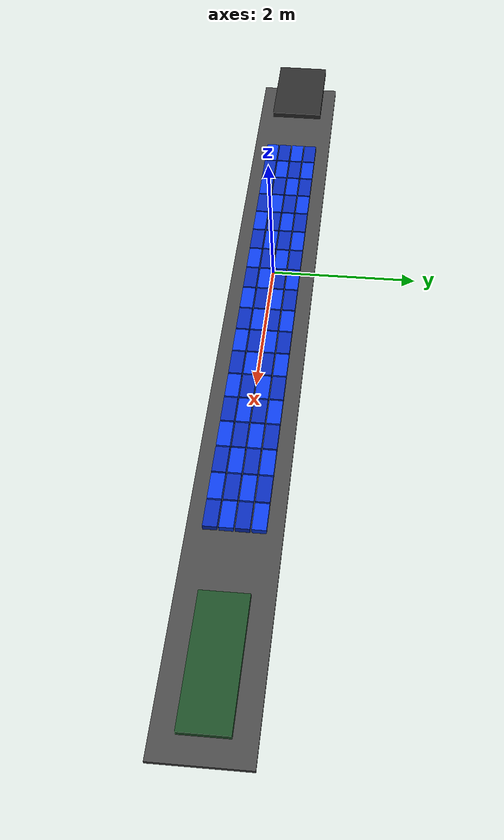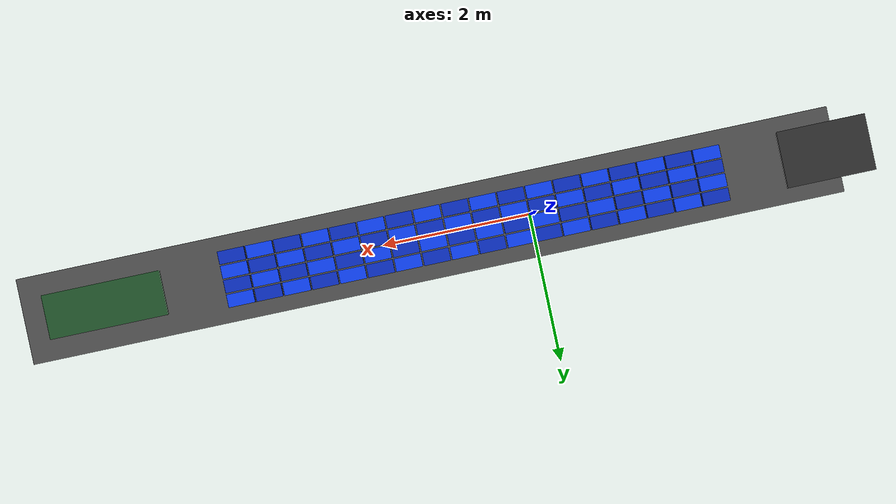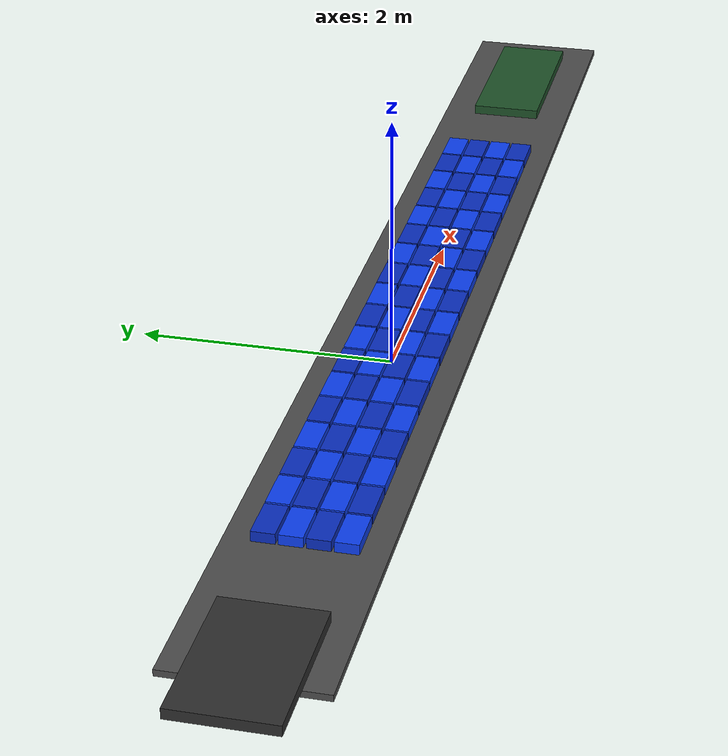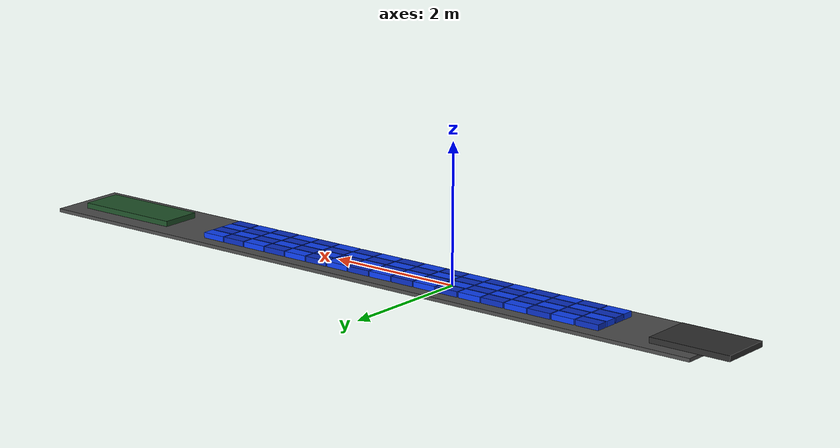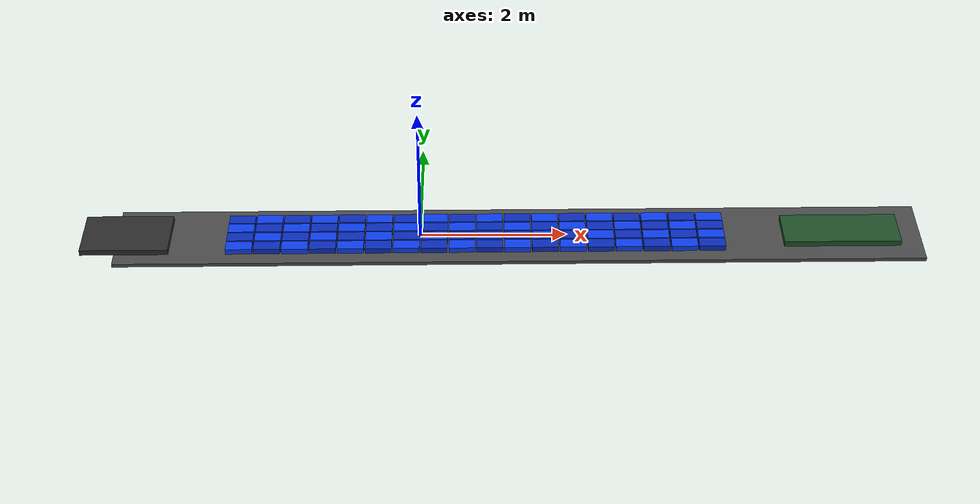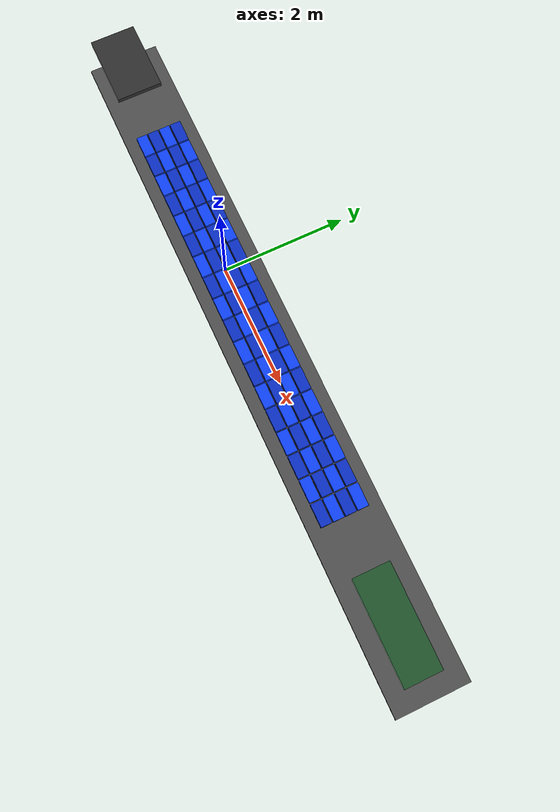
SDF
<?xml version="1.0"?>
<sdf version="1.10">
  <world name="matrix_14x4_stream">
    <gravity>0 0 -9.81</gravity>
    <physics name="physics_1ms" type="ignored">
      <max_step_size>0.001</max_step_size>
      <real_time_factor>1.0</real_time_factor>
      <real_time_update_rate>1000</real_time_update_rate>
    </physics>
    <plugin filename="gz-sim-physics-system" name="gz::sim::systems::Physics"/>
    <plugin filename="gz-sim-user-commands-system" name="gz::sim::systems::UserCommands"/>
    <plugin filename="gz-sim-scene-broadcaster-system" name="gz::sim::systems::SceneBroadcaster"/>
    <plugin filename="gz-sim-sensors-system" name="gz::sim::systems::Sensors">
      <render_engine>ogre2</render_engine>
    </plugin>
    <light type="directional" name="sun">
      <pose>0 0 6 0 0 0</pose><cast_shadows>false</cast_shadows>
      <diffuse>0.9 0.9 0.9 1</diffuse><specular>0.2 0.2 0.2 1</specular>
      <direction>-0.4 0.2 -1.0</direction>
    </light>
    <model name="platform">
      <static>true</static>
      <pose>1.355000 0 -0.025 0 0 0</pose>
      <link name="platform_link">
        <collision name="platform_collision"><geometry><box><size>11.050000 1.160000 0.05</size></box></geometry></collision>
        <visual name="platform_visual"><geometry><box><size>11.050000 1.160000 0.05</size></box></geometry>
          <material><ambient>0.20 0.20 0.20 1</ambient><diffuse>0.30 0.30 0.30 1</diffuse></material>
        </visual>
      </link>
    </model>

    <model name="infeed_conveyor">
      <static>true</static>
      <pose>-4.030000 0.000000 0 0 0 0</pose>
      <link name="belt">
        <pose>0 0 0.040000 0 0 0</pose>
        <collision name="belt_collision">
          <max_contacts>8</max_contacts>
          <geometry><box><size>1.200000 0.760000 0.080000</size></box></geometry>
          <surface><friction><ode>
            <mu>0.8</mu><mu2>0.8</mu2><fdir1>1 0 0</fdir1>
          </ode></friction></surface>
        </collision>
        <visual name="belt_visual">
          <geometry><box><size>1.200000 0.760000 0.080000</size></box></geometry>
          <material>
            <ambient>0.180 0.180 0.180 1</ambient>
            <diffuse>0.180 0.180 0.180 1</diffuse>
          </material>
        </visual>
      </link>

      <plugin filename="gz-sim-track-controller-system"
              name="gz::sim::systems::TrackController">
        <link>belt</link>
        <track_orientation>0 0 0</track_orientation>
        <velocity_topic>/singulator/infeed/cmd_vel</velocity_topic>
        <odometry_topic>/singulator/infeed/odometry</odometry_topic>
        <odometry_publish_frequency>1</odometry_publish_frequency>
        <min_velocity>-3.0</min_velocity>
        <max_velocity>3.0</max_velocity>
        <min_acceleration>-6.0</min_acceleration>
        <max_acceleration>6.0</max_acceleration>
        <min_jerk>-30.0</min_jerk>
        <max_jerk>30.0</max_jerk>
        <max_command_age>2.0</max_command_age>
      </plugin>

    </model>

    <model name="cell_r00_c00">
      <static>true</static>
      <pose>-2.470000 -0.292500 0 0 0 0</pose>
      <link name="belt">
        <pose>0 0 0.040000 0 0 0</pose>
        <collision name="belt_collision">
          <max_contacts>8</max_contacts>
          <geometry><box><size>0.360000 0.175000 0.080000</size></box></geometry>
          <surface><friction><ode>
            <mu>0.8</mu><mu2>0.8</mu2><fdir1>1 0 0</fdir1>
          </ode></friction></surface>
        </collision>
        <visual name="belt_visual">
          <geometry><box><size>0.360000 0.175000 0.080000</size></box></geometry>
          <material>
            <ambient>0.050 0.250 0.950 1</ambient>
            <diffuse>0.050 0.250 0.950 1</diffuse>
          </material>
        </visual>
      </link>

      <plugin filename="gz-sim-track-controller-system"
              name="gz::sim::systems::TrackController">
        <link>belt</link>
        <track_orientation>0 0 0</track_orientation>
        <velocity_topic>/singulator/cell/r00_c00/cmd_vel</velocity_topic>
        <odometry_topic>/singulator/cell/r00_c00/odometry</odometry_topic>
        <odometry_publish_frequency>1</odometry_publish_frequency>
        <min_velocity>-3.0</min_velocity>
        <max_velocity>3.0</max_velocity>
        <min_acceleration>-6.0</min_acceleration>
        <max_acceleration>6.0</max_acceleration>
        <min_jerk>-30.0</min_jerk>
        <max_jerk>30.0</max_jerk>
        <max_command_age>2.0</max_command_age>
      </plugin>

    </model>

    <model name="cell_r00_c01">
      <static>true</static>
      <pose>-2.470000 -0.097500 0 0 0 0</pose>
      <link name="belt">
        <pose>0 0 0.040000 0 0 0</pose>
        <collision name="belt_collision">
          <max_contacts>8</max_contacts>
          <geometry><box><size>0.360000 0.175000 0.080000</size></box></geometry>
          <surface><friction><ode>
            <mu>0.8</mu><mu2>0.8</mu2><fdir1>1 0 0</fdir1>
          </ode></friction></surface>
        </collision>
        <visual name="belt_visual">
          <geometry><box><size>0.360000 0.175000 0.080000</size></box></geometry>
          <material>
            <ambient>0.040 0.180 0.750 1</ambient>
            <diffuse>0.040 0.180 0.750 1</diffuse>
          </material>
        </visual>
      </link>

      <plugin filename="gz-sim-track-controller-system"
              name="gz::sim::systems::TrackController">
        <link>belt</link>
        <track_orientation>0 0 0</track_orientation>
        <velocity_topic>/singulator/cell/r00_c01/cmd_vel</velocity_topic>
        <odometry_topic>/singulator/cell/r00_c01/odometry</odometry_topic>
        <odometry_publish_frequency>1</odometry_publish_frequency>
        <min_velocity>-3.0</min_velocity>
        <max_velocity>3.0</max_velocity>
        <min_acceleration>-6.0</min_acceleration>
        <max_acceleration>6.0</max_acceleration>
        <min_jerk>-30.0</min_jerk>
        <max_jerk>30.0</max_jerk>
        <max_command_age>2.0</max_command_age>
      </plugin>

    </model>

    <model name="cell_r00_c02">
      <static>true</static>
      <pose>-2.470000 0.097500 0 0 0 0</pose>
      <link name="belt">
        <pose>0 0 0.040000 0 0 0</pose>
        <collision name="belt_collision">
          <max_contacts>8</max_contacts>
          <geometry><box><size>0.360000 0.175000 0.080000</size></box></geometry>
          <surface><friction><ode>
            <mu>0.8</mu><mu2>0.8</mu2><fdir1>1 0 0</fdir1>
          </ode></friction></surface>
        </collision>
        <visual name="belt_visual">
          <geometry><box><size>0.360000 0.175000 0.080000</size></box></geometry>
          <material>
            <ambient>0.050 0.250 0.950 1</ambient>
            <diffuse>0.050 0.250 0.950 1</diffuse>
          </material>
        </visual>
      </link>

      <plugin filename="gz-sim-track-controller-system"
              name="gz::sim::systems::TrackController">
        <link>belt</link>
        <track_orientation>0 0 0</track_orientation>
        <velocity_topic>/singulator/cell/r00_c02/cmd_vel</velocity_topic>
        <odometry_topic>/singulator/cell/r00_c02/odometry</odometry_topic>
        <odometry_publish_frequency>1</odometry_publish_frequency>
        <min_velocity>-3.0</min_velocity>
        <max_velocity>3.0</max_velocity>
        <min_acceleration>-6.0</min_acceleration>
        <max_acceleration>6.0</max_acceleration>
        <min_jerk>-30.0</min_jerk>
        <max_jerk>30.0</max_jerk>
        <max_command_age>2.0</max_command_age>
      </plugin>

    </model>

    <model name="cell_r00_c03">
      <static>true</static>
      <pose>-2.470000 0.292500 0 0 0 0</pose>
      <link name="belt">
        <pose>0 0 0.040000 0 0 0</pose>
        <collision name="belt_collision">
          <max_contacts>8</max_contacts>
          <geometry><box><size>0.360000 0.175000 0.080000</size></box></geometry>
          <surface><friction><ode>
            <mu>0.8</mu><mu2>0.8</mu2><fdir1>1 0 0</fdir1>
          </ode></friction></surface>
        </collision>
        <visual name="belt_visual">
          <geometry><box><size>0.360000 0.175000 0.080000</size></box></geometry>
          <material>
            <ambient>0.040 0.180 0.750 1</ambient>
            <diffuse>0.040 0.180 0.750 1</diffuse>
          </material>
        </visual>
      </link>

      <plugin filename="gz-sim-track-controller-system"
              name="gz::sim::systems::TrackController">
        <link>belt</link>
        <track_orientation>0 0 0</track_orientation>
        <velocity_topic>/singulator/cell/r00_c03/cmd_vel</velocity_topic>
        <odometry_topic>/singulator/cell/r00_c03/odometry</odometry_topic>
        <odometry_publish_frequency>1</odometry_publish_frequency>
        <min_velocity>-3.0</min_velocity>
        <max_velocity>3.0</max_velocity>
        <min_acceleration>-6.0</min_acceleration>
        <max_acceleration>6.0</max_acceleration>
        <min_jerk>-30.0</min_jerk>
        <max_jerk>30.0</max_jerk>
        <max_command_age>2.0</max_command_age>
      </plugin>

    </model>

    <model name="cell_r01_c00">
      <static>true</static>
      <pose>-2.090000 -0.292500 0 0 0 0</pose>
      <link name="belt">
        <pose>0 0 0.040000 0 0 0</pose>
        <collision name="belt_collision">
          <max_contacts>8</max_contacts>
          <geometry><box><size>0.360000 0.175000 0.080000</size></box></geometry>
          <surface><friction><ode>
            <mu>0.8</mu><mu2>0.8</mu2><fdir1>1 0 0</fdir1>
          </ode></friction></surface>
        </collision>
        <visual name="belt_visual">
          <geometry><box><size>0.360000 0.175000 0.080000</size></box></geometry>
          <material>
            <ambient>0.040 0.180 0.750 1</ambient>
            <diffuse>0.040 0.180 0.750 1</diffuse>
          </material>
        </visual>
      </link>

      <plugin filename="gz-sim-track-controller-system"
              name="gz::sim::systems::TrackController">
        <link>belt</link>
        <track_orientation>0 0 0</track_orientation>
        <velocity_topic>/singulator/cell/r01_c00/cmd_vel</velocity_topic>
        <odometry_topic>/singulator/cell/r01_c00/odometry</odometry_topic>
        <odometry_publish_frequency>1</odometry_publish_frequency>
        <min_velocity>-3.0</min_velocity>
        <max_velocity>3.0</max_velocity>
        <min_acceleration>-6.0</min_acceleration>
        <max_acceleration>6.0</max_acceleration>
        <min_jerk>-30.0</min_jerk>
        <max_jerk>30.0</max_jerk>
        <max_command_age>2.0</max_command_age>
      </plugin>

    </model>

    <model name="cell_r01_c01">
      <static>true</static>
      <pose>-2.090000 -0.097500 0 0 0 0</pose>
      <link name="belt">
        <pose>0 0 0.040000 0 0 0</pose>
        <collision name="belt_collision">
          <max_contacts>8</max_contacts>
          <geometry><box><size>0.360000 0.175000 0.080000</size></box></geometry>
          <surface><friction><ode>
            <mu>0.8</mu><mu2>0.8</mu2><fdir1>1 0 0</fdir1>
          </ode></friction></surface>
        </collision>
        <visual name="belt_visual">
          <geometry><box><size>0.360000 0.175000 0.080000</size></box></geometry>
          <material>
            <ambient>0.050 0.250 0.950 1</ambient>
            <diffuse>0.050 0.250 0.950 1</diffuse>
          </material>
        </visual>
      </link>

      <plugin filename="gz-sim-track-controller-system"
              name="gz::sim::systems::TrackController">
        <link>belt</link>
        <track_orientation>0 0 0</track_orientation>
        <velocity_topic>/singulator/cell/r01_c01/cmd_vel</velocity_topic>
        <odometry_topic>/singulator/cell/r01_c01/odometry</odometry_topic>
        <odometry_publish_frequency>1</odometry_publish_frequency>
        <min_velocity>-3.0</min_velocity>
        <max_velocity>3.0</max_velocity>
        <min_acceleration>-6.0</min_acceleration>
        <max_acceleration>6.0</max_acceleration>
        <min_jerk>-30.0</min_jerk>
        <max_jerk>30.0</max_jerk>
        <max_command_age>2.0</max_command_age>
      </plugin>

    </model>

    <model name="cell_r01_c02">
      <static>true</static>
      <pose>-2.090000 0.097500 0 0 0 0</pose>
      <link name="belt">
        <pose>0 0 0.040000 0 0 0</pose>
        <collision name="belt_collision">
          <max_contacts>8</max_contacts>
          <geometry><box><size>0.360000 0.175000 0.080000</size></box></geometry>
          <surface><friction><ode>
            <mu>0.8</mu><mu2>0.8</mu2><fdir1>1 0 0</fdir1>
          </ode></friction></surface>
        </collision>
        <visual name="belt_visual">
          <geometry><box><size>0.360000 0.175000 0.080000</size></box></geometry>
          <material>
            <ambient>0.040 0.180 0.750 1</ambient>
            <diffuse>0.040 0.180 0.750 1</diffuse>
          </material>
        </visual>
      </link>

      <plugin filename="gz-sim-track-controller-system"
              name="gz::sim::systems::TrackController">
        <link>belt</link>
        <track_orientation>0 0 0</track_orientation>
        <velocity_topic>/singulator/cell/r01_c02/cmd_vel</velocity_topic>
        <odometry_topic>/singulator/cell/r01_c02/odometry</odometry_topic>
        <odometry_publish_frequency>1</odometry_publish_frequency>
        <min_velocity>-3.0</min_velocity>
        <max_velocity>3.0</max_velocity>
        <min_acceleration>-6.0</min_acceleration>
        <max_acceleration>6.0</max_acceleration>
        <min_jerk>-30.0</min_jerk>
        <max_jerk>30.0</max_jerk>
        <max_command_age>2.0</max_command_age>
      </plugin>

    </model>

    <model name="cell_r01_c03">
      <static>true</static>
      <pose>-2.090000 0.292500 0 0 0 0</pose>
      <link name="belt">
        <pose>0 0 0.040000 0 0 0</pose>
        <collision name="belt_collision">
          <max_contacts>8</max_contacts>
          <geometry><box><size>0.360000 0.175000 0.080000</size></box></geometry>
          <surface><friction><ode>
            <mu>0.8</mu><mu2>0.8</mu2><fdir1>1 0 0</fdir1>
          </ode></friction></surface>
        </collision>
        <visual name="belt_visual">
          <geometry><box><size>0.360000 0.175000 0.080000</size></box></geometry>
          <material>
            <ambient>0.050 0.250 0.950 1</ambient>
            <diffuse>0.050 0.250 0.950 1</diffuse>
          </material>
        </visual>
      </link>

      <plugin filename="gz-sim-track-controller-system"
              name="gz::sim::systems::TrackController">
        <link>belt</link>
        <track_orientation>0 0 0</track_orientation>
        <velocity_topic>/singulator/cell/r01_c03/cmd_vel</velocity_topic>
        <odometry_topic>/singulator/cell/r01_c03/odometry</odometry_topic>
        <odometry_publish_frequency>1</odometry_publish_frequency>
        <min_velocity>-3.0</min_velocity>
        <max_velocity>3.0</max_velocity>
        <min_acceleration>-6.0</min_acceleration>
        <max_acceleration>6.0</max_acceleration>
        <min_jerk>-30.0</min_jerk>
        <max_jerk>30.0</max_jerk>
        <max_command_age>2.0</max_command_age>
      </plugin>

    </model>

    <model name="cell_r02_c00">
      <static>true</static>
      <pose>-1.710000 -0.292500 0 0 0 0</pose>
      <link name="belt">
        <pose>0 0 0.040000 0 0 0</pose>
        <collision name="belt_collision">
          <max_contacts>8</max_contacts>
          <geometry><box><size>0.360000 0.175000 0.080000</size></box></geometry>
          <surface><friction><ode>
            <mu>0.8</mu><mu2>0.8</mu2><fdir1>1 0 0</fdir1>
          </ode></friction></surface>
        </collision>
        <visual name="belt_visual">
          <geometry><box><size>0.360000 0.175000 0.080000</size></box></geometry>
          <material>
            <ambient>0.050 0.250 0.950 1</ambient>
            <diffuse>0.050 0.250 0.950 1</diffuse>
          </material>
        </visual>
      </link>

      <plugin filename="gz-sim-track-controller-system"
              name="gz::sim::systems::TrackController">
        <link>belt</link>
        <track_orientation>0 0 0</track_orientation>
        <velocity_topic>/singulator/cell/r02_c00/cmd_vel</velocity_topic>
        <odometry_topic>/singulator/cell/r02_c00/odometry</odometry_topic>
        <odometry_publish_frequency>1</odometry_publish_frequency>
        <min_velocity>-3.0</min_velocity>
        <max_velocity>3.0</max_velocity>
        <min_acceleration>-6.0</min_acceleration>
        <max_acceleration>6.0</max_acceleration>
        <min_jerk>-30.0</min_jerk>
        <max_jerk>30.0</max_jerk>
        <max_command_age>2.0</max_command_age>
      </plugin>

    </model>

    <model name="cell_r02_c01">
      <static>true</static>
      <pose>-1.710000 -0.097500 0 0 0 0</pose>
      <link name="belt">
        <pose>0 0 0.040000 0 0 0</pose>
        <collision name="belt_collision">
          <max_contacts>8</max_contacts>
          <geometry><box><size>0.360000 0.175000 0.080000</size></box></geometry>
          <surface><friction><ode>
            <mu>0.8</mu><mu2>0.8</mu2><fdir1>1 0 0</fdir1>
          </ode></friction></surface>
        </collision>
        <visual name="belt_visual">
          <geometry><box><size>0.360000 0.175000 0.080000</size></box></geometry>
          <material>
            <ambient>0.040 0.180 0.750 1</ambient>
            <diffuse>0.040 0.180 0.750 1</diffuse>
          </material>
        </visual>
      </link>

      <plugin filename="gz-sim-track-controller-system"
              name="gz::sim::systems::TrackController">
        <link>belt</link>
        <track_orientation>0 0 0</track_orientation>
        <velocity_topic>/singulator/cell/r02_c01/cmd_vel</velocity_topic>
        <odometry_topic>/singulator/cell/r02_c01/odometry</odometry_topic>
        <odometry_publish_frequency>1</odometry_publish_frequency>
        <min_velocity>-3.0</min_velocity>
        <max_velocity>3.0</max_velocity>
        <min_acceleration>-6.0</min_acceleration>
        <max_acceleration>6.0</max_acceleration>
        <min_jerk>-30.0</min_jerk>
        <max_jerk>30.0</max_jerk>
        <max_command_age>2.0</max_command_age>
      </plugin>

    </model>

    <model name="cell_r02_c02">
      <static>true</static>
      <pose>-1.710000 0.097500 0 0 0 0</pose>
      <link name="belt">
        <pose>0 0 0.040000 0 0 0</pose>
        <collision name="belt_collision">
          <max_contacts>8</max_contacts>
          <geometry><box><size>0.360000 0.175000 0.080000</size></box></geometry>
          <surface><friction><ode>
            <mu>0.8</mu><mu2>0.8</mu2><fdir1>1 0 0</fdir1>
          </ode></friction></surface>
        </collision>
        <visual name="belt_visual">
          <geometry><box><size>0.360000 0.175000 0.080000</size></box></geometry>
          <material>
            <ambient>0.050 0.250 0.950 1</ambient>
            <diffuse>0.050 0.250 0.950 1</diffuse>
          </material>
        </visual>
      </link>

      <plugin filename="gz-sim-track-controller-system"
              name="gz::sim::systems::TrackController">
        <link>belt</link>
        <track_orientation>0 0 0</track_orientation>
        <velocity_topic>/singulator/cell/r02_c02/cmd_vel</velocity_topic>
        <odometry_topic>/singulator/cell/r02_c02/odometry</odometry_topic>
        <odometry_publish_frequency>1</odometry_publish_frequency>
        <min_velocity>-3.0</min_velocity>
        <max_velocity>3.0</max_velocity>
        <min_acceleration>-6.0</min_acceleration>
        <max_acceleration>6.0</max_acceleration>
        <min_jerk>-30.0</min_jerk>
        <max_jerk>30.0</max_jerk>
        <max_command_age>2.0</max_command_age>
      </plugin>

    </model>

    <model name="cell_r02_c03">
      <static>true</static>
      <pose>-1.710000 0.292500 0 0 0 0</pose>
      <link name="belt">
        <pose>0 0 0.040000 0 0 0</pose>
        <collision name="belt_collision">
          <max_contacts>8</max_contacts>
          <geometry><box><size>0.360000 0.175000 0.080000</size></box></geometry>
          <surface><friction><ode>
            <mu>0.8</mu><mu2>0.8</mu2><fdir1>1 0 0</fdir1>
          </ode></friction></surface>
        </collision>
        <visual name="belt_visual">
          <geometry><box><size>0.360000 0.175000 0.080000</size></box></geometry>
          <material>
            <ambient>0.040 0.180 0.750 1</ambient>
            <diffuse>0.040 0.180 0.750 1</diffuse>
          </material>
        </visual>
      </link>

      <plugin filename="gz-sim-track-controller-system"
              name="gz::sim::systems::TrackController">
        <link>belt</link>
        <track_orientation>0 0 0</track_orientation>
        <velocity_topic>/singulator/cell/r02_c03/cmd_vel</velocity_topic>
        <odometry_topic>/singulator/cell/r02_c03/odometry</odometry_topic>
        <odometry_publish_frequency>1</odometry_publish_frequency>
        <min_velocity>-3.0</min_velocity>
        <max_velocity>3.0</max_velocity>
        <min_acceleration>-6.0</min_acceleration>
        <max_acceleration>6.0</max_acceleration>
        <min_jerk>-30.0</min_jerk>
        <max_jerk>30.0</max_jerk>
        <max_command_age>2.0</max_command_age>
      </plugin>

    </model>

    <model name="cell_r03_c00">
      <static>true</static>
      <pose>-1.330000 -0.292500 0 0 0 0</pose>
      <link name="belt">
        <pose>0 0 0.040000 0 0 0</pose>
        <collision name="belt_collision">
          <max_contacts>8</max_contacts>
          <geometry><box><size>0.360000 0.175000 0.080000</size></box></geometry>
          <surface><friction><ode>
            <mu>0.8</mu><mu2>0.8</mu2><fdir1>1 0 0</fdir1>
          </ode></friction></surface>
        </collision>
        <visual name="belt_visual">
          <geometry><box><size>0.360000 0.175000 0.080000</size></box></geometry>
          <material>
            <ambient>0.040 0.180 0.750 1</ambient>
            <diffuse>0.040 0.180 0.750 1</diffuse>
          </material>
        </visual>
      </link>

      <plugin filename="gz-sim-track-controller-system"
              name="gz::sim::systems::TrackController">
        <link>belt</link>
        <track_orientation>0 0 0</track_orientation>
        <velocity_topic>/singulator/cell/r03_c00/cmd_vel</velocity_topic>
        <odometry_topic>/singulator/cell/r03_c00/odometry</odometry_topic>
        <odometry_publish_frequency>1</odometry_publish_frequency>
        <min_velocity>-3.0</min_velocity>
        <max_velocity>3.0</max_velocity>
        <min_acceleration>-6.0</min_acceleration>
        <max_acceleration>6.0</max_acceleration>
        <min_jerk>-30.0</min_jerk>
        <max_jerk>30.0</max_jerk>
        <max_command_age>2.0</max_command_age>
      </plugin>

    </model>

    <model name="cell_r03_c01">
      <static>true</static>
      <pose>-1.330000 -0.097500 0 0 0 0</pose>
      <link name="belt">
        <pose>0 0 0.040000 0 0 0</pose>
        <collision name="belt_collision">
          <max_contacts>8</max_contacts>
          <geometry><box><size>0.360000 0.175000 0.080000</size></box></geometry>
          <surface><friction><ode>
            <mu>0.8</mu><mu2>0.8</mu2><fdir1>1 0 0</fdir1>
          </ode></friction></surface>
        </collision>
        <visual name="belt_visual">
          <geometry><box><size>0.360000 0.175000 0.080000</size></box></geometry>
          <material>
            <ambient>0.050 0.250 0.950 1</ambient>
            <diffuse>0.050 0.250 0.950 1</diffuse>
          </material>
        </visual>
      </link>

      <plugin filename="gz-sim-track-controller-system"
              name="gz::sim::systems::TrackController">
        <link>belt</link>
        <track_orientation>0 0 0</track_orientation>
        <velocity_topic>/singulator/cell/r03_c01/cmd_vel</velocity_topic>
        <odometry_topic>/singulator/cell/r03_c01/odometry</odometry_topic>
        <odometry_publish_frequency>1</odometry_publish_frequency>
        <min_velocity>-3.0</min_velocity>
        <max_velocity>3.0</max_velocity>
        <min_acceleration>-6.0</min_acceleration>
        <max_acceleration>6.0</max_acceleration>
        <min_jerk>-30.0</min_jerk>
        <max_jerk>30.0</max_jerk>
        <max_command_age>2.0</max_command_age>
      </plugin>

    </model>

    <model name="cell_r03_c02">
      <static>true</static>
      <pose>-1.330000 0.097500 0 0 0 0</pose>
      <link name="belt">
        <pose>0 0 0.040000 0 0 0</pose>
        <collision name="belt_collision">
          <max_contacts>8</max_contacts>
          <geometry><box><size>0.360000 0.175000 0.080000</size></box></geometry>
          <surface><friction><ode>
            <mu>0.8</mu><mu2>0.8</mu2><fdir1>1 0 0</fdir1>
          </ode></friction></surface>
        </collision>
        <visual name="belt_visual">
          <geometry><box><size>0.360000 0.175000 0.080000</size></box></geometry>
          <material>
            <ambient>0.040 0.180 0.750 1</ambient>
            <diffuse>0.040 0.180 0.750 1</diffuse>
          </material>
        </visual>
      </link>

      <plugin filename="gz-sim-track-controller-system"
              name="gz::sim::systems::TrackController">
        <link>belt</link>
        <track_orientation>0 0 0</track_orientation>
        <velocity_topic>/singulator/cell/r03_c02/cmd_vel</velocity_topic>
        <odometry_topic>/singulator/cell/r03_c02/odometry</odometry_topic>
        <odometry_publish_frequency>1</odometry_publish_frequency>
        <min_velocity>-3.0</min_velocity>
        <max_velocity>3.0</max_velocity>
        <min_acceleration>-6.0</min_acceleration>
        <max_acceleration>6.0</max_acceleration>
        <min_jerk>-30.0</min_jerk>
        <max_jerk>30.0</max_jerk>
        <max_command_age>2.0</max_command_age>
      </plugin>

    </model>

    <model name="cell_r03_c03">
      <static>true</static>
      <pose>-1.330000 0.292500 0 0 0 0</pose>
      <link name="belt">
        <pose>0 0 0.040000 0 0 0</pose>
        <collision name="belt_collision">
          <max_contacts>8</max_contacts>
          <geometry><box><size>0.360000 0.175000 0.080000</size></box></geometry>
          <surface><friction><ode>
            <mu>0.8</mu><mu2>0.8</mu2><fdir1>1 0 0</fdir1>
          </ode></friction></surface>
        </collision>
        <visual name="belt_visual">
          <geometry><box><size>0.360000 0.175000 0.080000</size></box></geometry>
          <material>
            <ambient>0.050 0.250 0.950 1</ambient>
            <diffuse>0.050 0.250 0.950 1</diffuse>
          </material>
        </visual>
      </link>

      <plugin filename="gz-sim-track-controller-system"
              name="gz::sim::systems::TrackController">
        <link>belt</link>
        <track_orientation>0 0 0</track_orientation>
        <velocity_topic>/singulator/cell/r03_c03/cmd_vel</velocity_topic>
        <odometry_topic>/singulator/cell/r03_c03/odometry</odometry_topic>
        <odometry_publish_frequency>1</odometry_publish_frequency>
        <min_velocity>-3.0</min_velocity>
        <max_velocity>3.0</max_velocity>
        <min_acceleration>-6.0</min_acceleration>
        <max_acceleration>6.0</max_acceleration>
        <min_jerk>-30.0</min_jerk>
        <max_jerk>30.0</max_jerk>
        <max_command_age>2.0</max_command_age>
      </plugin>

    </model>

    <model name="cell_r04_c00">
      <static>true</static>
      <pose>-0.950000 -0.292500 0 0 0 0</pose>
      <link name="belt">
        <pose>0 0 0.040000 0 0 0</pose>
        <collision name="belt_collision">
          <max_contacts>8</max_contacts>
          <geometry><box><size>0.360000 0.175000 0.080000</size></box></geometry>
          <surface><friction><ode>
            <mu>0.8</mu><mu2>0.8</mu2><fdir1>1 0 0</fdir1>
          </ode></friction></surface>
        </collision>
        <visual name="belt_visual">
          <geometry><box><size>0.360000 0.175000 0.080000</size></box></geometry>
          <material>
            <ambient>0.050 0.250 0.950 1</ambient>
            <diffuse>0.050 0.250 0.950 1</diffuse>
          </material>
        </visual>
      </link>

      <plugin filename="gz-sim-track-controller-system"
              name="gz::sim::systems::TrackController">
        <link>belt</link>
        <track_orientation>0 0 0</track_orientation>
        <velocity_topic>/singulator/cell/r04_c00/cmd_vel</velocity_topic>
        <odometry_topic>/singulator/cell/r04_c00/odometry</odometry_topic>
        <odometry_publish_frequency>1</odometry_publish_frequency>
        <min_velocity>-3.0</min_velocity>
        <max_velocity>3.0</max_velocity>
        <min_acceleration>-6.0</min_acceleration>
        <max_acceleration>6.0</max_acceleration>
        <min_jerk>-30.0</min_jerk>
        <max_jerk>30.0</max_jerk>
        <max_command_age>2.0</max_command_age>
      </plugin>

    </model>

    <model name="cell_r04_c01">
      <static>true</static>
      <pose>-0.950000 -0.097500 0 0 0 0</pose>
      <link name="belt">
        <pose>0 0 0.040000 0 0 0</pose>
        <collision name="belt_collision">
          <max_contacts>8</max_contacts>
          <geometry><box><size>0.360000 0.175000 0.080000</size></box></geometry>
          <surface><friction><ode>
            <mu>0.8</mu><mu2>0.8</mu2><fdir1>1 0 0</fdir1>
          </ode></friction></surface>
        </collision>
        <visual name="belt_visual">
          <geometry><box><size>0.360000 0.175000 0.080000</size></box></geometry>
          <material>
            <ambient>0.040 0.180 0.750 1</ambient>
            <diffuse>0.040 0.180 0.750 1</diffuse>
          </material>
        </visual>
      </link>

      <plugin filename="gz-sim-track-controller-system"
              name="gz::sim::systems::TrackController">
        <link>belt</link>
        <track_orientation>0 0 0</track_orientation>
        <velocity_topic>/singulator/cell/r04_c01/cmd_vel</velocity_topic>
        <odometry_topic>/singulator/cell/r04_c01/odometry</odometry_topic>
        <odometry_publish_frequency>1</odometry_publish_frequency>
        <min_velocity>-3.0</min_velocity>
        <max_velocity>3.0</max_velocity>
        <min_acceleration>-6.0</min_acceleration>
        <max_acceleration>6.0</max_acceleration>
        <min_jerk>-30.0</min_jerk>
        <max_jerk>30.0</max_jerk>
        <max_command_age>2.0</max_command_age>
      </plugin>

    </model>

    <model name="cell_r04_c02">
      <static>true</static>
      <pose>-0.950000 0.097500 0 0 0 0</pose>
      <link name="belt">
        <pose>0 0 0.040000 0 0 0</pose>
        <collision name="belt_collision">
          <max_contacts>8</max_contacts>
          <geometry><box><size>0.360000 0.175000 0.080000</size></box></geometry>
          <surface><friction><ode>
            <mu>0.8</mu><mu2>0.8</mu2><fdir1>1 0 0</fdir1>
          </ode></friction></surface>
        </collision>
        <visual name="belt_visual">
          <geometry><box><size>0.360000 0.175000 0.080000</size></box></geometry>
          <material>
            <ambient>0.050 0.250 0.950 1</ambient>
            <diffuse>0.050 0.250 0.950 1</diffuse>
          </material>
        </visual>
      </link>

      <plugin filename="gz-sim-track-controller-system"
              name="gz::sim::systems::TrackController">
        <link>belt</link>
        <track_orientation>0 0 0</track_orientation>
        <velocity_topic>/singulator/cell/r04_c02/cmd_vel</velocity_topic>
        <odometry_topic>/singulator/cell/r04_c02/odometry</odometry_topic>
        <odometry_publish_frequency>1</odometry_publish_frequency>
        <min_velocity>-3.0</min_velocity>
        <max_velocity>3.0</max_velocity>
        <min_acceleration>-6.0</min_acceleration>
        <max_acceleration>6.0</max_acceleration>
        <min_jerk>-30.0</min_jerk>
        <max_jerk>30.0</max_jerk>
        <max_command_age>2.0</max_command_age>
      </plugin>

    </model>

    <model name="cell_r04_c03">
      <static>true</static>
      <pose>-0.950000 0.292500 0 0 0 0</pose>
      <link name="belt">
        <pose>0 0 0.040000 0 0 0</pose>
        <collision name="belt_collision">
          <max_contacts>8</max_contacts>
          <geometry><box><size>0.360000 0.175000 0.080000</size></box></geometry>
          <surface><friction><ode>
            <mu>0.8</mu><mu2>0.8</mu2><fdir1>1 0 0</fdir1>
          </ode></friction></surface>
        </collision>
        <visual name="belt_visual">
          <geometry><box><size>0.360000 0.175000 0.080000</size></box></geometry>
          <material>
            <ambient>0.040 0.180 0.750 1</ambient>
            <diffuse>0.040 0.180 0.750 1</diffuse>
          </material>
        </visual>
      </link>

      <plugin filename="gz-sim-track-controller-system"
              name="gz::sim::systems::TrackController">
        <link>belt</link>
        <track_orientation>0 0 0</track_orientation>
        <velocity_topic>/singulator/cell/r04_c03/cmd_vel</velocity_topic>
        <odometry_topic>/singulator/cell/r04_c03/odometry</odometry_topic>
        <odometry_publish_frequency>1</odometry_publish_frequency>
        <min_velocity>-3.0</min_velocity>
        <max_velocity>3.0</max_velocity>
        <min_acceleration>-6.0</min_acceleration>
        <max_acceleration>6.0</max_acceleration>
        <min_jerk>-30.0</min_jerk>
        <max_jerk>30.0</max_jerk>
        <max_command_age>2.0</max_command_age>
      </plugin>

    </model>

    <model name="cell_r05_c00">
      <static>true</static>
      <pose>-0.570000 -0.292500 0 0 0 0</pose>
      <link name="belt">
        <pose>0 0 0.040000 0 0 0</pose>
        <collision name="belt_collision">
          <max_contacts>8</max_contacts>
          <geometry><box><size>0.360000 0.175000 0.080000</size></box></geometry>
          <surface><friction><ode>
            <mu>0.8</mu><mu2>0.8</mu2><fdir1>1 0 0</fdir1>
          </ode></friction></surface>
        </collision>
        <visual name="belt_visual">
          <geometry><box><size>0.360000 0.175000 0.080000</size></box></geometry>
          <material>
            <ambient>0.040 0.180 0.750 1</ambient>
            <diffuse>0.040 0.180 0.750 1</diffuse>
          </material>
        </visual>
      </link>

      <plugin filename="gz-sim-track-controller-system"
              name="gz::sim::systems::TrackController">
        <link>belt</link>
        <track_orientation>0 0 0</track_orientation>
        <velocity_topic>/singulator/cell/r05_c00/cmd_vel</velocity_topic>
        <odometry_topic>/singulator/cell/r05_c00/odometry</odometry_topic>
        <odometry_publish_frequency>1</odometry_publish_frequency>
        <min_velocity>-3.0</min_velocity>
        <max_velocity>3.0</max_velocity>
        <min_acceleration>-6.0</min_acceleration>
        <max_acceleration>6.0</max_acceleration>
        <min_jerk>-30.0</min_jerk>
        <max_jerk>30.0</max_jerk>
        <max_command_age>2.0</max_command_age>
      </plugin>

    </model>

    <model name="cell_r05_c01">
      <static>true</static>
      <pose>-0.570000 -0.097500 0 0 0 0</pose>
      <link name="belt">
        <pose>0 0 0.040000 0 0 0</pose>
        <collision name="belt_collision">
          <max_contacts>8</max_contacts>
          <geometry><box><size>0.360000 0.175000 0.080000</size></box></geometry>
          <surface><friction><ode>
            <mu>0.8</mu><mu2>0.8</mu2><fdir1>1 0 0</fdir1>
          </ode></friction></surface>
        </collision>
        <visual name="belt_visual">
          <geometry><box><size>0.360000 0.175000 0.080000</size></box></geometry>
          <material>
            <ambient>0.050 0.250 0.950 1</ambient>
            <diffuse>0.050 0.250 0.950 1</diffuse>
          </material>
        </visual>
      </link>

      <plugin filename="gz-sim-track-controller-system"
              name="gz::sim::systems::TrackController">
        <link>belt</link>
        <track_orientation>0 0 0</track_orientation>
        <velocity_topic>/singulator/cell/r05_c01/cmd_vel</velocity_topic>
        <odometry_topic>/singulator/cell/r05_c01/odometry</odometry_topic>
        <odometry_publish_frequency>1</odometry_publish_frequency>
        <min_velocity>-3.0</min_velocity>
        <max_velocity>3.0</max_velocity>
        <min_acceleration>-6.0</min_acceleration>
        <max_acceleration>6.0</max_acceleration>
        <min_jerk>-30.0</min_jerk>
        <max_jerk>30.0</max_jerk>
        <max_command_age>2.0</max_command_age>
      </plugin>

    </model>

    <model name="cell_r05_c02">
      <static>true</static>
      <pose>-0.570000 0.097500 0 0 0 0</pose>
      <link name="belt">
        <pose>0 0 0.040000 0 0 0</pose>
        <collision name="belt_collision">
          <max_contacts>8</max_contacts>
          <geometry><box><size>0.360000 0.175000 0.080000</size></box></geometry>
          <surface><friction><ode>
            <mu>0.8</mu><mu2>0.8</mu2><fdir1>1 0 0</fdir1>
          </ode></friction></surface>
        </collision>
        <visual name="belt_visual">
          <geometry><box><size>0.360000 0.175000 0.080000</size></box></geometry>
          <material>
            <ambient>0.040 0.180 0.750 1</ambient>
            <diffuse>0.040 0.180 0.750 1</diffuse>
          </material>
        </visual>
      </link>

      <plugin filename="gz-sim-track-controller-system"
              name="gz::sim::systems::TrackController">
        <link>belt</link>
        <track_orientation>0 0 0</track_orientation>
        <velocity_topic>/singulator/cell/r05_c02/cmd_vel</velocity_topic>
        <odometry_topic>/singulator/cell/r05_c02/odometry</odometry_topic>
        <odometry_publish_frequency>1</odometry_publish_frequency>
        <min_velocity>-3.0</min_velocity>
        <max_velocity>3.0</max_velocity>
        <min_acceleration>-6.0</min_acceleration>
        <max_acceleration>6.0</max_acceleration>
        <min_jerk>-30.0</min_jerk>
        <max_jerk>30.0</max_jerk>
        <max_command_age>2.0</max_command_age>
      </plugin>

    </model>

    <model name="cell_r05_c03">
      <static>true</static>
      <pose>-0.570000 0.292500 0 0 0 0</pose>
      <link name="belt">
        <pose>0 0 0.040000 0 0 0</pose>
        <collision name="belt_collision">
          <max_contacts>8</max_contacts>
          <geometry><box><size>0.360000 0.175000 0.080000</size></box></geometry>
          <surface><friction><ode>
            <mu>0.8</mu><mu2>0.8</mu2><fdir1>1 0 0</fdir1>
          </ode></friction></surface>
        </collision>
        <visual name="belt_visual">
          <geometry><box><size>0.360000 0.175000 0.080000</size></box></geometry>
          <material>
            <ambient>0.050 0.250 0.950 1</ambient>
            <diffuse>0.050 0.250 0.950 1</diffuse>
          </material>
        </visual>
      </link>

      <plugin filename="gz-sim-track-controller-system"
              name="gz::sim::systems::TrackController">
        <link>belt</link>
        <track_orientation>0 0 0</track_orientation>
        <velocity_topic>/singulator/cell/r05_c03/cmd_vel</velocity_topic>
        <odometry_topic>/singulator/cell/r05_c03/odometry</odometry_topic>
        <odometry_publish_frequency>1</odometry_publish_frequency>
        <min_velocity>-3.0</min_velocity>
        <max_velocity>3.0</max_velocity>
        <min_acceleration>-6.0</min_acceleration>
        <max_acceleration>6.0</max_acceleration>
        <min_jerk>-30.0</min_jerk>
        <max_jerk>30.0</max_jerk>
        <max_command_age>2.0</max_command_age>
      </plugin>

    </model>

    <model name="cell_r06_c00">
      <static>true</static>
      <pose>-0.190000 -0.292500 0 0 0 0</pose>
      <link name="belt">
        <pose>0 0 0.040000 0 0 0</pose>
        <collision name="belt_collision">
          <max_contacts>8</max_contacts>
          <geometry><box><size>0.360000 0.175000 0.080000</size></box></geometry>
          <surface><friction><ode>
            <mu>0.8</mu><mu2>0.8</mu2><fdir1>1 0 0</fdir1>
          </ode></friction></surface>
        </collision>
        <visual name="belt_visual">
          <geometry><box><size>0.360000 0.175000 0.080000</size></box></geometry>
          <material>
            <ambient>0.050 0.250 0.950 1</ambient>
            <diffuse>0.050 0.250 0.950 1</diffuse>
          </material>
        </visual>
      </link>

      <plugin filename="gz-sim-track-controller-system"
              name="gz::sim::systems::TrackController">
        <link>belt</link>
        <track_orientation>0 0 0</track_orientation>
        <velocity_topic>/singulator/cell/r06_c00/cmd_vel</velocity_topic>
        <odometry_topic>/singulator/cell/r06_c00/odometry</odometry_topic>
        <odometry_publish_frequency>1</odometry_publish_frequency>
        <min_velocity>-3.0</min_velocity>
        <max_velocity>3.0</max_velocity>
        <min_acceleration>-6.0</min_acceleration>
        <max_acceleration>6.0</max_acceleration>
        <min_jerk>-30.0</min_jerk>
        <max_jerk>30.0</max_jerk>
        <max_command_age>2.0</max_command_age>
      </plugin>

    </model>

    <model name="cell_r06_c01">
      <static>true</static>
      <pose>-0.190000 -0.097500 0 0 0 0</pose>
      <link name="belt">
        <pose>0 0 0.040000 0 0 0</pose>
        <collision name="belt_collision">
          <max_contacts>8</max_contacts>
          <geometry><box><size>0.360000 0.175000 0.080000</size></box></geometry>
          <surface><friction><ode>
            <mu>0.8</mu><mu2>0.8</mu2><fdir1>1 0 0</fdir1>
          </ode></friction></surface>
        </collision>
        <visual name="belt_visual">
          <geometry><box><size>0.360000 0.175000 0.080000</size></box></geometry>
          <material>
            <ambient>0.040 0.180 0.750 1</ambient>
            <diffuse>0.040 0.180 0.750 1</diffuse>
          </material>
        </visual>
      </link>

      <plugin filename="gz-sim-track-controller-system"
              name="gz::sim::systems::TrackController">
        <link>belt</link>
        <track_orientation>0 0 0</track_orientation>
        <velocity_topic>/singulator/cell/r06_c01/cmd_vel</velocity_topic>
        <odometry_topic>/singulator/cell/r06_c01/odometry</odometry_topic>
        <odometry_publish_frequency>1</odometry_publish_frequency>
        <min_velocity>-3.0</min_velocity>
        <max_velocity>3.0</max_velocity>
        <min_acceleration>-6.0</min_acceleration>
        <max_acceleration>6.0</max_acceleration>
        <min_jerk>-30.0</min_jerk>
        <max_jerk>30.0</max_jerk>
        <max_command_age>2.0</max_command_age>
      </plugin>

    </model>

    <model name="cell_r06_c02">
      <static>true</static>
      <pose>-0.190000 0.097500 0 0 0 0</pose>
      <link name="belt">
        <pose>0 0 0.040000 0 0 0</pose>
        <collision name="belt_collision">
          <max_contacts>8</max_contacts>
          <geometry><box><size>0.360000 0.175000 0.080000</size></box></geometry>
          <surface><friction><ode>
            <mu>0.8</mu><mu2>0.8</mu2><fdir1>1 0 0</fdir1>
          </ode></friction></surface>
        </collision>
        <visual name="belt_visual">
          <geometry><box><size>0.360000 0.175000 0.080000</size></box></geometry>
          <material>
            <ambient>0.050 0.250 0.950 1</ambient>
            <diffuse>0.050 0.250 0.950 1</diffuse>
          </material>
        </visual>
      </link>

      <plugin filename="gz-sim-track-controller-system"
              name="gz::sim::systems::TrackController">
        <link>belt</link>
        <track_orientation>0 0 0</track_orientation>
        <velocity_topic>/singulator/cell/r06_c02/cmd_vel</velocity_topic>
        <odometry_topic>/singulator/cell/r06_c02/odometry</odometry_topic>
        <odometry_publish_frequency>1</odometry_publish_frequency>
        <min_velocity>-3.0</min_velocity>
        <max_velocity>3.0</max_velocity>
        <min_acceleration>-6.0</min_acceleration>
        <max_acceleration>6.0</max_acceleration>
        <min_jerk>-30.0</min_jerk>
        <max_jerk>30.0</max_jerk>
        <max_command_age>2.0</max_command_age>
      </plugin>

    </model>

    <model name="cell_r06_c03">
      <static>true</static>
      <pose>-0.190000 0.292500 0 0 0 0</pose>
      <link name="belt">
        <pose>0 0 0.040000 0 0 0</pose>
        <collision name="belt_collision">
          <max_contacts>8</max_contacts>
          <geometry><box><size>0.360000 0.175000 0.080000</size></box></geometry>
          <surface><friction><ode>
            <mu>0.8</mu><mu2>0.8</mu2><fdir1>1 0 0</fdir1>
          </ode></friction></surface>
        </collision>
        <visual name="belt_visual">
          <geometry><box><size>0.360000 0.175000 0.080000</size></box></geometry>
          <material>
            <ambient>0.040 0.180 0.750 1</ambient>
            <diffuse>0.040 0.180 0.750 1</diffuse>
          </material>
        </visual>
      </link>

      <plugin filename="gz-sim-track-controller-system"
              name="gz::sim::systems::TrackController">
        <link>belt</link>
        <track_orientation>0 0 0</track_orientation>
        <velocity_topic>/singulator/cell/r06_c03/cmd_vel</velocity_topic>
        <odometry_topic>/singulator/cell/r06_c03/odometry</odometry_topic>
        <odometry_publish_frequency>1</odometry_publish_frequency>
        <min_velocity>-3.0</min_velocity>
        <max_velocity>3.0</max_velocity>
        <min_acceleration>-6.0</min_acceleration>
        <max_acceleration>6.0</max_acceleration>
        <min_jerk>-30.0</min_jerk>
        <max_jerk>30.0</max_jerk>
        <max_command_age>2.0</max_command_age>
      </plugin>

    </model>

    <model name="cell_r07_c00">
      <static>true</static>
      <pose>0.190000 -0.292500 0 0 0 0</pose>
      <link name="belt">
        <pose>0 0 0.040000 0 0 0</pose>
        <collision name="belt_collision">
          <max_contacts>8</max_contacts>
          <geometry><box><size>0.360000 0.175000 0.080000</size></box></geometry>
          <surface><friction><ode>
            <mu>0.8</mu><mu2>0.8</mu2><fdir1>1 0 0</fdir1>
          </ode></friction></surface>
        </collision>
        <visual name="belt_visual">
          <geometry><box><size>0.360000 0.175000 0.080000</size></box></geometry>
          <material>
            <ambient>0.040 0.180 0.750 1</ambient>
            <diffuse>0.040 0.180 0.750 1</diffuse>
          </material>
        </visual>
      </link>

      <plugin filename="gz-sim-track-controller-system"
              name="gz::sim::systems::TrackController">
        <link>belt</link>
        <track_orientation>0 0 0</track_orientation>
        <velocity_topic>/singulator/cell/r07_c00/cmd_vel</velocity_topic>
        <odometry_topic>/singulator/cell/r07_c00/odometry</odometry_topic>
        <odometry_publish_frequency>1</odometry_publish_frequency>
        <min_velocity>-3.0</min_velocity>
        <max_velocity>3.0</max_velocity>
        <min_acceleration>-6.0</min_acceleration>
        <max_acceleration>6.0</max_acceleration>
        <min_jerk>-30.0</min_jerk>
        <max_jerk>30.0</max_jerk>
        <max_command_age>2.0</max_command_age>
      </plugin>

    </model>

    <model name="cell_r07_c01">
      <static>true</static>
      <pose>0.190000 -0.097500 0 0 0 0</pose>
      <link name="belt">
        <pose>0 0 0.040000 0 0 0</pose>
        <collision name="belt_collision">
          <max_contacts>8</max_contacts>
          <geometry><box><size>0.360000 0.175000 0.080000</size></box></geometry>
          <surface><friction><ode>
            <mu>0.8</mu><mu2>0.8</mu2><fdir1>1 0 0</fdir1>
          </ode></friction></surface>
        </collision>
        <visual name="belt_visual">
          <geometry><box><size>0.360000 0.175000 0.080000</size></box></geometry>
          <material>
            <ambient>0.050 0.250 0.950 1</ambient>
            <diffuse>0.050 0.250 0.950 1</diffuse>
          </material>
        </visual>
      </link>

      <plugin filename="gz-sim-track-controller-system"
              name="gz::sim::systems::TrackController">
        <link>belt</link>
        <track_orientation>0 0 0</track_orientation>
        <velocity_topic>/singulator/cell/r07_c01/cmd_vel</velocity_topic>
        <odometry_topic>/singulator/cell/r07_c01/odometry</odometry_topic>
        <odometry_publish_frequency>1</odometry_publish_frequency>
        <min_velocity>-3.0</min_velocity>
        <max_velocity>3.0</max_velocity>
        <min_acceleration>-6.0</min_acceleration>
        <max_acceleration>6.0</max_acceleration>
        <min_jerk>-30.0</min_jerk>
        <max_jerk>30.0</max_jerk>
        <max_command_age>2.0</max_command_age>
      </plugin>

    </model>

    <model name="cell_r07_c02">
      <static>true</static>
      <pose>0.190000 0.097500 0 0 0 0</pose>
      <link name="belt">
        <pose>0 0 0.040000 0 0 0</pose>
        <collision name="belt_collision">
          <max_contacts>8</max_contacts>
          <geometry><box><size>0.360000 0.175000 0.080000</size></box></geometry>
          <surface><friction><ode>
            <mu>0.8</mu><mu2>0.8</mu2><fdir1>1 0 0</fdir1>
          </ode></friction></surface>
        </collision>
        <visual name="belt_visual">
          <geometry><box><size>0.360000 0.175000 0.080000</size></box></geometry>
          <material>
            <ambient>0.040 0.180 0.750 1</ambient>
            <diffuse>0.040 0.180 0.750 1</diffuse>
          </material>
        </visual>
      </link>

      <plugin filename="gz-sim-track-controller-system"
              name="gz::sim::systems::TrackController">
        <link>belt</link>
        <track_orientation>0 0 0</track_orientation>
        <velocity_topic>/singulator/cell/r07_c02/cmd_vel</velocity_topic>
        <odometry_topic>/singulator/cell/r07_c02/odometry</odometry_topic>
        <odometry_publish_frequency>1</odometry_publish_frequency>
        <min_velocity>-3.0</min_velocity>
        <max_velocity>3.0</max_velocity>
        <min_acceleration>-6.0</min_acceleration>
        <max_acceleration>6.0</max_acceleration>
        <min_jerk>-30.0</min_jerk>
        <max_jerk>30.0</max_jerk>
        <max_command_age>2.0</max_command_age>
      </plugin>

    </model>

    <model name="cell_r07_c03">
      <static>true</static>
      <pose>0.190000 0.292500 0 0 0 0</pose>
      <link name="belt">
        <pose>0 0 0.040000 0 0 0</pose>
        <collision name="belt_collision">
          <max_contacts>8</max_contacts>
          <geometry><box><size>0.360000 0.175000 0.080000</size></box></geometry>
          <surface><friction><ode>
            <mu>0.8</mu><mu2>0.8</mu2><fdir1>1 0 0</fdir1>
          </ode></friction></surface>
        </collision>
        <visual name="belt_visual">
          <geometry><box><size>0.360000 0.175000 0.080000</size></box></geometry>
          <material>
            <ambient>0.050 0.250 0.950 1</ambient>
            <diffuse>0.050 0.250 0.950 1</diffuse>
          </material>
        </visual>
      </link>

      <plugin filename="gz-sim-track-controller-system"
              name="gz::sim::systems::TrackController">
        <link>belt</link>
        <track_orientation>0 0 0</track_orientation>
        <velocity_topic>/singulator/cell/r07_c03/cmd_vel</velocity_topic>
        <odometry_topic>/singulator/cell/r07_c03/odometry</odometry_topic>
        <odometry_publish_frequency>1</odometry_publish_frequency>
        <min_velocity>-3.0</min_velocity>
        <max_velocity>3.0</max_velocity>
        <min_acceleration>-6.0</min_acceleration>
        <max_acceleration>6.0</max_acceleration>
        <min_jerk>-30.0</min_jerk>
        <max_jerk>30.0</max_jerk>
        <max_command_age>2.0</max_command_age>
      </plugin>

    </model>

    <model name="cell_r08_c00">
      <static>true</static>
      <pose>0.570000 -0.292500 0 0 0 0</pose>
      <link name="belt">
        <pose>0 0 0.040000 0 0 0</pose>
        <collision name="belt_collision">
          <max_contacts>8</max_contacts>
          <geometry><box><size>0.360000 0.175000 0.080000</size></box></geometry>
          <surface><friction><ode>
            <mu>0.8</mu><mu2>0.8</mu2><fdir1>1 0 0</fdir1>
          </ode></friction></surface>
        </collision>
        <visual name="belt_visual">
          <geometry><box><size>0.360000 0.175000 0.080000</size></box></geometry>
          <material>
            <ambient>0.050 0.250 0.950 1</ambient>
            <diffuse>0.050 0.250 0.950 1</diffuse>
          </material>
        </visual>
      </link>

      <plugin filename="gz-sim-track-controller-system"
              name="gz::sim::systems::TrackController">
        <link>belt</link>
        <track_orientation>0 0 0</track_orientation>
        <velocity_topic>/singulator/cell/r08_c00/cmd_vel</velocity_topic>
        <odometry_topic>/singulator/cell/r08_c00/odometry</odometry_topic>
        <odometry_publish_frequency>1</odometry_publish_frequency>
        <min_velocity>-3.0</min_velocity>
        <max_velocity>3.0</max_velocity>
        <min_acceleration>-6.0</min_acceleration>
        <max_acceleration>6.0</max_acceleration>
        <min_jerk>-30.0</min_jerk>
        <max_jerk>30.0</max_jerk>
        <max_command_age>2.0</max_command_age>
      </plugin>

    </model>

    <model name="cell_r08_c01">
      <static>true</static>
      <pose>0.570000 -0.097500 0 0 0 0</pose>
      <link name="belt">
        <pose>0 0 0.040000 0 0 0</pose>
        <collision name="belt_collision">
          <max_contacts>8</max_contacts>
          <geometry><box><size>0.360000 0.175000 0.080000</size></box></geometry>
          <surface><friction><ode>
            <mu>0.8</mu><mu2>0.8</mu2><fdir1>1 0 0</fdir1>
          </ode></friction></surface>
        </collision>
        <visual name="belt_visual">
          <geometry><box><size>0.360000 0.175000 0.080000</size></box></geometry>
          <material>
            <ambient>0.040 0.180 0.750 1</ambient>
            <diffuse>0.040 0.180 0.750 1</diffuse>
          </material>
        </visual>
      </link>

      <plugin filename="gz-sim-track-controller-system"
              name="gz::sim::systems::TrackController">
        <link>belt</link>
        <track_orientation>0 0 0</track_orientation>
        <velocity_topic>/singulator/cell/r08_c01/cmd_vel</velocity_topic>
        <odometry_topic>/singulator/cell/r08_c01/odometry</odometry_topic>
        <odometry_publish_frequency>1</odometry_publish_frequency>
        <min_velocity>-3.0</min_velocity>
        <max_velocity>3.0</max_velocity>
        <min_acceleration>-6.0</min_acceleration>
        <max_acceleration>6.0</max_acceleration>
        <min_jerk>-30.0</min_jerk>
        <max_jerk>30.0</max_jerk>
        <max_command_age>2.0</max_command_age>
      </plugin>

    </model>

    <model name="cell_r08_c02">
      <static>true</static>
      <pose>0.570000 0.097500 0 0 0 0</pose>
      <link name="belt">
        <pose>0 0 0.040000 0 0 0</pose>
        <collision name="belt_collision">
          <max_contacts>8</max_contacts>
          <geometry><box><size>0.360000 0.175000 0.080000</size></box></geometry>
          <surface><friction><ode>
            <mu>0.8</mu><mu2>0.8</mu2><fdir1>1 0 0</fdir1>
          </ode></friction></surface>
        </collision>
        <visual name="belt_visual">
          <geometry><box><size>0.360000 0.175000 0.080000</size></box></geometry>
          <material>
            <ambient>0.050 0.250 0.950 1</ambient>
            <diffuse>0.050 0.250 0.950 1</diffuse>
          </material>
        </visual>
      </link>

      <plugin filename="gz-sim-track-controller-system"
              name="gz::sim::systems::TrackController">
        <link>belt</link>
        <track_orientation>0 0 0</track_orientation>
        <velocity_topic>/singulator/cell/r08_c02/cmd_vel</velocity_topic>
        <odometry_topic>/singulator/cell/r08_c02/odometry</odometry_topic>
        <odometry_publish_frequency>1</odometry_publish_frequency>
        <min_velocity>-3.0</min_velocity>
        <max_velocity>3.0</max_velocity>
        <min_acceleration>-6.0</min_acceleration>
        <max_acceleration>6.0</max_acceleration>
        <min_jerk>-30.0</min_jerk>
        <max_jerk>30.0</max_jerk>
        <max_command_age>2.0</max_command_age>
      </plugin>

    </model>

    <model name="cell_r08_c03">
      <static>true</static>
      <pose>0.570000 0.292500 0 0 0 0</pose>
      <link name="belt">
        <pose>0 0 0.040000 0 0 0</pose>
        <collision name="belt_collision">
          <max_contacts>8</max_contacts>
          <geometry><box><size>0.360000 0.175000 0.080000</size></box></geometry>
          <surface><friction><ode>
            <mu>0.8</mu><mu2>0.8</mu2><fdir1>1 0 0</fdir1>
          </ode></friction></surface>
        </collision>
        <visual name="belt_visual">
          <geometry><box><size>0.360000 0.175000 0.080000</size></box></geometry>
          <material>
            <ambient>0.040 0.180 0.750 1</ambient>
            <diffuse>0.040 0.180 0.750 1</diffuse>
          </material>
        </visual>
      </link>

      <plugin filename="gz-sim-track-controller-system"
              name="gz::sim::systems::TrackController">
        <link>belt</link>
        <track_orientation>0 0 0</track_orientation>
        <velocity_topic>/singulator/cell/r08_c03/cmd_vel</velocity_topic>
        <odometry_topic>/singulator/cell/r08_c03/odometry</odometry_topic>
        <odometry_publish_frequency>1</odometry_publish_frequency>
        <min_velocity>-3.0</min_velocity>
        <max_velocity>3.0</max_velocity>
        <min_acceleration>-6.0</min_acceleration>
        <max_acceleration>6.0</max_acceleration>
        <min_jerk>-30.0</min_jerk>
        <max_jerk>30.0</max_jerk>
        <max_command_age>2.0</max_command_age>
      </plugin>

    </model>

    <model name="cell_r09_c00">
      <static>true</static>
      <pose>0.950000 -0.292500 0 0 0 0</pose>
      <link name="belt">
        <pose>0 0 0.040000 0 0 0</pose>
        <collision name="belt_collision">
          <max_contacts>8</max_contacts>
          <geometry><box><size>0.360000 0.175000 0.080000</size></box></geometry>
          <surface><friction><ode>
            <mu>0.8</mu><mu2>0.8</mu2><fdir1>1 0 0</fdir1>
          </ode></friction></surface>
        </collision>
        <visual name="belt_visual">
          <geometry><box><size>0.360000 0.175000 0.080000</size></box></geometry>
          <material>
            <ambient>0.040 0.180 0.750 1</ambient>
            <diffuse>0.040 0.180 0.750 1</diffuse>
          </material>
        </visual>
      </link>

      <plugin filename="gz-sim-track-controller-system"
              name="gz::sim::systems::TrackController">
        <link>belt</link>
        <track_orientation>0 0 0</track_orientation>
        <velocity_topic>/singulator/cell/r09_c00/cmd_vel</velocity_topic>
        <odometry_topic>/singulator/cell/r09_c00/odometry</odometry_topic>
        <odometry_publish_frequency>1</odometry_publish_frequency>
        <min_velocity>-3.0</min_velocity>
        <max_velocity>3.0</max_velocity>
        <min_acceleration>-6.0</min_acceleration>
        <max_acceleration>6.0</max_acceleration>
        <min_jerk>-30.0</min_jerk>
        <max_jerk>30.0</max_jerk>
        <max_command_age>2.0</max_command_age>
      </plugin>

    </model>

    <model name="cell_r09_c01">
      <static>true</static>
      <pose>0.950000 -0.097500 0 0 0 0</pose>
      <link name="belt">
        <pose>0 0 0.040000 0 0 0</pose>
        <collision name="belt_collision">
          <max_contacts>8</max_contacts>
          <geometry><box><size>0.360000 0.175000 0.080000</size></box></geometry>
          <surface><friction><ode>
            <mu>0.8</mu><mu2>0.8</mu2><fdir1>1 0 0</fdir1>
          </ode></friction></surface>
        </collision>
        <visual name="belt_visual">
          <geometry><box><size>0.360000 0.175000 0.080000</size></box></geometry>
          <material>
            <ambient>0.050 0.250 0.950 1</ambient>
            <diffuse>0.050 0.250 0.950 1</diffuse>
          </material>
        </visual>
      </link>

      <plugin filename="gz-sim-track-controller-system"
              name="gz::sim::systems::TrackController">
        <link>belt</link>
        <track_orientation>0 0 0</track_orientation>
        <velocity_topic>/singulator/cell/r09_c01/cmd_vel</velocity_topic>
        <odometry_topic>/singulator/cell/r09_c01/odometry</odometry_topic>
        <odometry_publish_frequency>1</odometry_publish_frequency>
        <min_velocity>-3.0</min_velocity>
        <max_velocity>3.0</max_velocity>
        <min_acceleration>-6.0</min_acceleration>
        <max_acceleration>6.0</max_acceleration>
        <min_jerk>-30.0</min_jerk>
        <max_jerk>30.0</max_jerk>
        <max_command_age>2.0</max_command_age>
      </plugin>

    </model>

    <model name="cell_r09_c02">
      <static>true</static>
      <pose>0.950000 0.097500 0 0 0 0</pose>
      <link name="belt">
        <pose>0 0 0.040000 0 0 0</pose>
        <collision name="belt_collision">
          <max_contacts>8</max_contacts>
          <geometry><box><size>0.360000 0.175000 0.080000</size></box></geometry>
          <surface><friction><ode>
            <mu>0.8</mu><mu2>0.8</mu2><fdir1>1 0 0</fdir1>
          </ode></friction></surface>
        </collision>
        <visual name="belt_visual">
          <geometry><box><size>0.360000 0.175000 0.080000</size></box></geometry>
          <material>
            <ambient>0.040 0.180 0.750 1</ambient>
            <diffuse>0.040 0.180 0.750 1</diffuse>
          </material>
        </visual>
      </link>

      <plugin filename="gz-sim-track-controller-system"
              name="gz::sim::systems::TrackController">
        <link>belt</link>
        <track_orientation>0 0 0</track_orientation>
        <velocity_topic>/singulator/cell/r09_c02/cmd_vel</velocity_topic>
        <odometry_topic>/singulator/cell/r09_c02/odometry</odometry_topic>
        <odometry_publish_frequency>1</odometry_publish_frequency>
        <min_velocity>-3.0</min_velocity>
        <max_velocity>3.0</max_velocity>
        <min_acceleration>-6.0</min_acceleration>
        <max_acceleration>6.0</max_acceleration>
        <min_jerk>-30.0</min_jerk>
        <max_jerk>30.0</max_jerk>
        <max_command_age>2.0</max_command_age>
      </plugin>

    </model>

    <model name="cell_r09_c03">
      <static>true</static>
      <pose>0.950000 0.292500 0 0 0 0</pose>
      <link name="belt">
        <pose>0 0 0.040000 0 0 0</pose>
        <collision name="belt_collision">
          <max_contacts>8</max_contacts>
          <geometry><box><size>0.360000 0.175000 0.080000</size></box></geometry>
          <surface><friction><ode>
            <mu>0.8</mu><mu2>0.8</mu2><fdir1>1 0 0</fdir1>
          </ode></friction></surface>
        </collision>
        <visual name="belt_visual">
          <geometry><box><size>0.360000 0.175000 0.080000</size></box></geometry>
          <material>
            <ambient>0.050 0.250 0.950 1</ambient>
            <diffuse>0.050 0.250 0.950 1</diffuse>
          </material>
        </visual>
      </link>

      <plugin filename="gz-sim-track-controller-system"
              name="gz::sim::systems::TrackController">
        <link>belt</link>
        <track_orientation>0 0 0</track_orientation>
        <velocity_topic>/singulator/cell/r09_c03/cmd_vel</velocity_topic>
        <odometry_topic>/singulator/cell/r09_c03/odometry</odometry_topic>
        <odometry_publish_frequency>1</odometry_publish_frequency>
        <min_velocity>-3.0</min_velocity>
        <max_velocity>3.0</max_velocity>
        <min_acceleration>-6.0</min_acceleration>
        <max_acceleration>6.0</max_acceleration>
        <min_jerk>-30.0</min_jerk>
        <max_jerk>30.0</max_jerk>
        <max_command_age>2.0</max_command_age>
      </plugin>

    </model>

    <model name="cell_r10_c00">
      <static>true</static>
      <pose>1.330000 -0.292500 0 0 0 0</pose>
      <link name="belt">
        <pose>0 0 0.040000 0 0 0</pose>
        <collision name="belt_collision">
          <max_contacts>8</max_contacts>
          <geometry><box><size>0.360000 0.175000 0.080000</size></box></geometry>
          <surface><friction><ode>
            <mu>0.8</mu><mu2>0.8</mu2><fdir1>1 0 0</fdir1>
          </ode></friction></surface>
        </collision>
        <visual name="belt_visual">
          <geometry><box><size>0.360000 0.175000 0.080000</size></box></geometry>
          <material>
            <ambient>0.050 0.250 0.950 1</ambient>
            <diffuse>0.050 0.250 0.950 1</diffuse>
          </material>
        </visual>
      </link>

      <plugin filename="gz-sim-track-controller-system"
              name="gz::sim::systems::TrackController">
        <link>belt</link>
        <track_orientation>0 0 0</track_orientation>
        <velocity_topic>/singulator/cell/r10_c00/cmd_vel</velocity_topic>
        <odometry_topic>/singulator/cell/r10_c00/odometry</odometry_topic>
        <odometry_publish_frequency>1</odometry_publish_frequency>
        <min_velocity>-3.0</min_velocity>
        <max_velocity>3.0</max_velocity>
        <min_acceleration>-6.0</min_acceleration>
        <max_acceleration>6.0</max_acceleration>
        <min_jerk>-30.0</min_jerk>
        <max_jerk>30.0</max_jerk>
        <max_command_age>2.0</max_command_age>
      </plugin>

    </model>

    <model name="cell_r10_c01">
      <static>true</static>
      <pose>1.330000 -0.097500 0 0 0 0</pose>
      <link name="belt">
        <pose>0 0 0.040000 0 0 0</pose>
        <collision name="belt_collision">
          <max_contacts>8</max_contacts>
          <geometry><box><size>0.360000 0.175000 0.080000</size></box></geometry>
          <surface><friction><ode>
            <mu>0.8</mu><mu2>0.8</mu2><fdir1>1 0 0</fdir1>
          </ode></friction></surface>
        </collision>
        <visual name="belt_visual">
          <geometry><box><size>0.360000 0.175000 0.080000</size></box></geometry>
          <material>
            <ambient>0.040 0.180 0.750 1</ambient>
            <diffuse>0.040 0.180 0.750 1</diffuse>
          </material>
        </visual>
      </link>

      <plugin filename="gz-sim-track-controller-system"
              name="gz::sim::systems::TrackController">
        <link>belt</link>
        <track_orientation>0 0 0</track_orientation>
        <velocity_topic>/singulator/cell/r10_c01/cmd_vel</velocity_topic>
        <odometry_topic>/singulator/cell/r10_c01/odometry</odometry_topic>
        <odometry_publish_frequency>1</odometry_publish_frequency>
        <min_velocity>-3.0</min_velocity>
        <max_velocity>3.0</max_velocity>
        <min_acceleration>-6.0</min_acceleration>
        <max_acceleration>6.0</max_acceleration>
        <min_jerk>-30.0</min_jerk>
        <max_jerk>30.0</max_jerk>
        <max_command_age>2.0</max_command_age>
      </plugin>

    </model>

    <model name="cell_r10_c02">
      <static>true</static>
      <pose>1.330000 0.097500 0 0 0 0</pose>
      <link name="belt">
        <pose>0 0 0.040000 0 0 0</pose>
        <collision name="belt_collision">
          <max_contacts>8</max_contacts>
          <geometry><box><size>0.360000 0.175000 0.080000</size></box></geometry>
          <surface><friction><ode>
            <mu>0.8</mu><mu2>0.8</mu2><fdir1>1 0 0</fdir1>
          </ode></friction></surface>
        </collision>
        <visual name="belt_visual">
          <geometry><box><size>0.360000 0.175000 0.080000</size></box></geometry>
          <material>
            <ambient>0.050 0.250 0.950 1</ambient>
            <diffuse>0.050 0.250 0.950 1</diffuse>
          </material>
        </visual>
      </link>

      <plugin filename="gz-sim-track-controller-system"
              name="gz::sim::systems::TrackController">
        <link>belt</link>
        <track_orientation>0 0 0</track_orientation>
        <velocity_topic>/singulator/cell/r10_c02/cmd_vel</velocity_topic>
        <odometry_topic>/singulator/cell/r10_c02/odometry</odometry_topic>
        <odometry_publish_frequency>1</odometry_publish_frequency>
        <min_velocity>-3.0</min_velocity>
        <max_velocity>3.0</max_velocity>
        <min_acceleration>-6.0</min_acceleration>
        <max_acceleration>6.0</max_acceleration>
        <min_jerk>-30.0</min_jerk>
        <max_jerk>30.0</max_jerk>
        <max_command_age>2.0</max_command_age>
      </plugin>

    </model>

    <model name="cell_r10_c03">
      <static>true</static>
      <pose>1.330000 0.292500 0 0 0 0</pose>
      <link name="belt">
        <pose>0 0 0.040000 0 0 0</pose>
        <collision name="belt_collision">
          <max_contacts>8</max_contacts>
          <geometry><box><size>0.360000 0.175000 0.080000</size></box></geometry>
          <surface><friction><ode>
            <mu>0.8</mu><mu2>0.8</mu2><fdir1>1 0 0</fdir1>
          </ode></friction></surface>
        </collision>
        <visual name="belt_visual">
          <geometry><box><size>0.360000 0.175000 0.080000</size></box></geometry>
          <material>
            <ambient>0.040 0.180 0.750 1</ambient>
            <diffuse>0.040 0.180 0.750 1</diffuse>
          </material>
        </visual>
      </link>

      <plugin filename="gz-sim-track-controller-system"
              name="gz::sim::systems::TrackController">
        <link>belt</link>
        <track_orientation>0 0 0</track_orientation>
        <velocity_topic>/singulator/cell/r10_c03/cmd_vel</velocity_topic>
        <odometry_topic>/singulator/cell/r10_c03/odometry</odometry_topic>
        <odometry_publish_frequency>1</odometry_publish_frequency>
        <min_velocity>-3.0</min_velocity>
        <max_velocity>3.0</max_velocity>
        <min_acceleration>-6.0</min_acceleration>
        <max_acceleration>6.0</max_acceleration>
        <min_jerk>-30.0</min_jerk>
        <max_jerk>30.0</max_jerk>
        <max_command_age>2.0</max_command_age>
      </plugin>

    </model>

    <model name="cell_r11_c00">
      <static>true</static>
      <pose>1.710000 -0.292500 0 0 0 0</pose>
      <link name="belt">
        <pose>0 0 0.040000 0 0 0</pose>
        <collision name="belt_collision">
          <max_contacts>8</max_contacts>
          <geometry><box><size>0.360000 0.175000 0.080000</size></box></geometry>
          <surface><friction><ode>
            <mu>0.8</mu><mu2>0.8</mu2><fdir1>1 0 0</fdir1>
          </ode></friction></surface>
        </collision>
        <visual name="belt_visual">
          <geometry><box><size>0.360000 0.175000 0.080000</size></box></geometry>
          <material>
            <ambient>0.040 0.180 0.750 1</ambient>
            <diffuse>0.040 0.180 0.750 1</diffuse>
          </material>
        </visual>
      </link>

      <plugin filename="gz-sim-track-controller-system"
              name="gz::sim::systems::TrackController">
        <link>belt</link>
        <track_orientation>0 0 0</track_orientation>
        <velocity_topic>/singulator/cell/r11_c00/cmd_vel</velocity_topic>
        <odometry_topic>/singulator/cell/r11_c00/odometry</odometry_topic>
        <odometry_publish_frequency>1</odometry_publish_frequency>
        <min_velocity>-3.0</min_velocity>
        <max_velocity>3.0</max_velocity>
        <min_acceleration>-6.0</min_acceleration>
        <max_acceleration>6.0</max_acceleration>
        <min_jerk>-30.0</min_jerk>
        <max_jerk>30.0</max_jerk>
        <max_command_age>2.0</max_command_age>
      </plugin>

    </model>

    <model name="cell_r11_c01">
      <static>true</static>
      <pose>1.710000 -0.097500 0 0 0 0</pose>
      <link name="belt">
        <pose>0 0 0.040000 0 0 0</pose>
        <collision name="belt_collision">
          <max_contacts>8</max_contacts>
          <geometry><box><size>0.360000 0.175000 0.080000</size></box></geometry>
          <surface><friction><ode>
            <mu>0.8</mu><mu2>0.8</mu2><fdir1>1 0 0</fdir1>
          </ode></friction></surface>
        </collision>
        <visual name="belt_visual">
          <geometry><box><size>0.360000 0.175000 0.080000</size></box></geometry>
          <material>
            <ambient>0.050 0.250 0.950 1</ambient>
            <diffuse>0.050 0.250 0.950 1</diffuse>
          </material>
        </visual>
      </link>

      <plugin filename="gz-sim-track-controller-system"
              name="gz::sim::systems::TrackController">
        <link>belt</link>
        <track_orientation>0 0 0</track_orientation>
        <velocity_topic>/singulator/cell/r11_c01/cmd_vel</velocity_topic>
        <odometry_topic>/singulator/cell/r11_c01/odometry</odometry_topic>
        <odometry_publish_frequency>1</odometry_publish_frequency>
        <min_velocity>-3.0</min_velocity>
        <max_velocity>3.0</max_velocity>
        <min_acceleration>-6.0</min_acceleration>
        <max_acceleration>6.0</max_acceleration>
        <min_jerk>-30.0</min_jerk>
        <max_jerk>30.0</max_jerk>
        <max_command_age>2.0</max_command_age>
      </plugin>

    </model>

    <model name="cell_r11_c02">
      <static>true</static>
      <pose>1.710000 0.097500 0 0 0 0</pose>
      <link name="belt">
        <pose>0 0 0.040000 0 0 0</pose>
        <collision name="belt_collision">
          <max_contacts>8</max_contacts>
          <geometry><box><size>0.360000 0.175000 0.080000</size></box></geometry>
          <surface><friction><ode>
            <mu>0.8</mu><mu2>0.8</mu2><fdir1>1 0 0</fdir1>
          </ode></friction></surface>
        </collision>
        <visual name="belt_visual">
          <geometry><box><size>0.360000 0.175000 0.080000</size></box></geometry>
          <material>
            <ambient>0.040 0.180 0.750 1</ambient>
            <diffuse>0.040 0.180 0.750 1</diffuse>
          </material>
        </visual>
      </link>

      <plugin filename="gz-sim-track-controller-system"
              name="gz::sim::systems::TrackController">
        <link>belt</link>
        <track_orientation>0 0 0</track_orientation>
        <velocity_topic>/singulator/cell/r11_c02/cmd_vel</velocity_topic>
        <odometry_topic>/singulator/cell/r11_c02/odometry</odometry_topic>
        <odometry_publish_frequency>1</odometry_publish_frequency>
        <min_velocity>-3.0</min_velocity>
        <max_velocity>3.0</max_velocity>
        <min_acceleration>-6.0</min_acceleration>
        <max_acceleration>6.0</max_acceleration>
        <min_jerk>-30.0</min_jerk>
        <max_jerk>30.0</max_jerk>
        <max_command_age>2.0</max_command_age>
      </plugin>

    </model>

    <model name="cell_r11_c03">
      <static>true</static>
      <pose>1.710000 0.292500 0 0 0 0</pose>
      <link name="belt">
        <pose>0 0 0.040000 0 0 0</pose>
        <collision name="belt_collision">
          <max_contacts>8</max_contacts>
          <geometry><box><size>0.360000 0.175000 0.080000</size></box></geometry>
          <surface><friction><ode>
            <mu>0.8</mu><mu2>0.8</mu2><fdir1>1 0 0</fdir1>
          </ode></friction></surface>
        </collision>
        <visual name="belt_visual">
          <geometry><box><size>0.360000 0.175000 0.080000</size></box></geometry>
          <material>
            <ambient>0.050 0.250 0.950 1</ambient>
            <diffuse>0.050 0.250 0.950 1</diffuse>
          </material>
        </visual>
      </link>

      <plugin filename="gz-sim-track-controller-system"
              name="gz::sim::systems::TrackController">
        <link>belt</link>
        <track_orientation>0 0 0</track_orientation>
        <velocity_topic>/singulator/cell/r11_c03/cmd_vel</velocity_topic>
        <odometry_topic>/singulator/cell/r11_c03/odometry</odometry_topic>
        <odometry_publish_frequency>1</odometry_publish_frequency>
        <min_velocity>-3.0</min_velocity>
        <max_velocity>3.0</max_velocity>
        <min_acceleration>-6.0</min_acceleration>
        <max_acceleration>6.0</max_acceleration>
        <min_jerk>-30.0</min_jerk>
        <max_jerk>30.0</max_jerk>
        <max_command_age>2.0</max_command_age>
      </plugin>

    </model>

    <model name="cell_r12_c00">
      <static>true</static>
      <pose>2.090000 -0.292500 0 0 0 0</pose>
      <link name="belt">
        <pose>0 0 0.040000 0 0 0</pose>
        <collision name="belt_collision">
          <max_contacts>8</max_contacts>
          <geometry><box><size>0.360000 0.175000 0.080000</size></box></geometry>
          <surface><friction><ode>
            <mu>0.8</mu><mu2>0.8</mu2><fdir1>1 0 0</fdir1>
          </ode></friction></surface>
        </collision>
        <visual name="belt_visual">
          <geometry><box><size>0.360000 0.175000 0.080000</size></box></geometry>
          <material>
            <ambient>0.050 0.250 0.950 1</ambient>
            <diffuse>0.050 0.250 0.950 1</diffuse>
          </material>
        </visual>
      </link>

      <plugin filename="gz-sim-track-controller-system"
              name="gz::sim::systems::TrackController">
        <link>belt</link>
        <track_orientation>0 0 0</track_orientation>
        <velocity_topic>/singulator/cell/r12_c00/cmd_vel</velocity_topic>
        <odometry_topic>/singulator/cell/r12_c00/odometry</odometry_topic>
        <odometry_publish_frequency>1</odometry_publish_frequency>
        <min_velocity>-3.0</min_velocity>
        <max_velocity>3.0</max_velocity>
        <min_acceleration>-6.0</min_acceleration>
        <max_acceleration>6.0</max_acceleration>
        <min_jerk>-30.0</min_jerk>
        <max_jerk>30.0</max_jerk>
        <max_command_age>2.0</max_command_age>
      </plugin>

    </model>

    <model name="cell_r12_c01">
      <static>true</static>
      <pose>2.090000 -0.097500 0 0 0 0</pose>
      <link name="belt">
        <pose>0 0 0.040000 0 0 0</pose>
        <collision name="belt_collision">
          <max_contacts>8</max_contacts>
          <geometry><box><size>0.360000 0.175000 0.080000</size></box></geometry>
          <surface><friction><ode>
            <mu>0.8</mu><mu2>0.8</mu2><fdir1>1 0 0</fdir1>
          </ode></friction></surface>
        </collision>
        <visual name="belt_visual">
          <geometry><box><size>0.360000 0.175000 0.080000</size></box></geometry>
          <material>
            <ambient>0.040 0.180 0.750 1</ambient>
            <diffuse>0.040 0.180 0.750 1</diffuse>
          </material>
        </visual>
      </link>

      <plugin filename="gz-sim-track-controller-system"
              name="gz::sim::systems::TrackController">
        <link>belt</link>
        <track_orientation>0 0 0</track_orientation>
        <velocity_topic>/singulator/cell/r12_c01/cmd_vel</velocity_topic>
        <odometry_topic>/singulator/cell/r12_c01/odometry</odometry_topic>
        <odometry_publish_frequency>1</odometry_publish_frequency>
        <min_velocity>-3.0</min_velocity>
        <max_velocity>3.0</max_velocity>
        <min_acceleration>-6.0</min_acceleration>
        <max_acceleration>6.0</max_acceleration>
        <min_jerk>-30.0</min_jerk>
        <max_jerk>30.0</max_jerk>
        <max_command_age>2.0</max_command_age>
      </plugin>

    </model>

    <model name="cell_r12_c02">
      <static>true</static>
      <pose>2.090000 0.097500 0 0 0 0</pose>
      <link name="belt">
        <pose>0 0 0.040000 0 0 0</pose>
        <collision name="belt_collision">
          <max_contacts>8</max_contacts>
          <geometry><box><size>0.360000 0.175000 0.080000</size></box></geometry>
          <surface><friction><ode>
            <mu>0.8</mu><mu2>0.8</mu2><fdir1>1 0 0</fdir1>
          </ode></friction></surface>
        </collision>
        <visual name="belt_visual">
          <geometry><box><size>0.360000 0.175000 0.080000</size></box></geometry>
          <material>
            <ambient>0.050 0.250 0.950 1</ambient>
            <diffuse>0.050 0.250 0.950 1</diffuse>
          </material>
        </visual>
      </link>

      <plugin filename="gz-sim-track-controller-system"
              name="gz::sim::systems::TrackController">
        <link>belt</link>
        <track_orientation>0 0 0</track_orientation>
        <velocity_topic>/singulator/cell/r12_c02/cmd_vel</velocity_topic>
        <odometry_topic>/singulator/cell/r12_c02/odometry</odometry_topic>
        <odometry_publish_frequency>1</odometry_publish_frequency>
        <min_velocity>-3.0</min_velocity>
        <max_velocity>3.0</max_velocity>
        <min_acceleration>-6.0</min_acceleration>
        <max_acceleration>6.0</max_acceleration>
        <min_jerk>-30.0</min_jerk>
        <max_jerk>30.0</max_jerk>
        <max_command_age>2.0</max_command_age>
      </plugin>

    </model>

    <model name="cell_r12_c03">
      <static>true</static>
      <pose>2.090000 0.292500 0 0 0 0</pose>
      <link name="belt">
        <pose>0 0 0.040000 0 0 0</pose>
        <collision name="belt_collision">
          <max_contacts>8</max_contacts>
          <geometry><box><size>0.360000 0.175000 0.080000</size></box></geometry>
          <surface><friction><ode>
            <mu>0.8</mu><mu2>0.8</mu2><fdir1>1 0 0</fdir1>
          </ode></friction></surface>
        </collision>
        <visual name="belt_visual">
          <geometry><box><size>0.360000 0.175000 0.080000</size></box></geometry>
          <material>
            <ambient>0.040 0.180 0.750 1</ambient>
            <diffuse>0.040 0.180 0.750 1</diffuse>
          </material>
        </visual>
      </link>

      <plugin filename="gz-sim-track-controller-system"
              name="gz::sim::systems::TrackController">
        <link>belt</link>
        <track_orientation>0 0 0</track_orientation>
        <velocity_topic>/singulator/cell/r12_c03/cmd_vel</velocity_topic>
        <odometry_topic>/singulator/cell/r12_c03/odometry</odometry_topic>
        <odometry_publish_frequency>1</odometry_publish_frequency>
        <min_velocity>-3.0</min_velocity>
        <max_velocity>3.0</max_velocity>
        <min_acceleration>-6.0</min_acceleration>
        <max_acceleration>6.0</max_acceleration>
        <min_jerk>-30.0</min_jerk>
        <max_jerk>30.0</max_jerk>
        <max_command_age>2.0</max_command_age>
      </plugin>

    </model>

    <model name="cell_r13_c00">
      <static>true</static>
      <pose>2.470000 -0.292500 0 0 0 0</pose>
      <link name="belt">
        <pose>0 0 0.040000 0 0 0</pose>
        <collision name="belt_collision">
          <max_contacts>8</max_contacts>
          <geometry><box><size>0.360000 0.175000 0.080000</size></box></geometry>
          <surface><friction><ode>
            <mu>0.8</mu><mu2>0.8</mu2><fdir1>1 0 0</fdir1>
          </ode></friction></surface>
        </collision>
        <visual name="belt_visual">
          <geometry><box><size>0.360000 0.175000 0.080000</size></box></geometry>
          <material>
            <ambient>0.040 0.180 0.750 1</ambient>
            <diffuse>0.040 0.180 0.750 1</diffuse>
          </material>
        </visual>
      </link>

      <plugin filename="gz-sim-track-controller-system"
              name="gz::sim::systems::TrackController">
        <link>belt</link>
        <track_orientation>0 0 0</track_orientation>
        <velocity_topic>/singulator/cell/r13_c00/cmd_vel</velocity_topic>
        <odometry_topic>/singulator/cell/r13_c00/odometry</odometry_topic>
        <odometry_publish_frequency>1</odometry_publish_frequency>
        <min_velocity>-3.0</min_velocity>
        <max_velocity>3.0</max_velocity>
        <min_acceleration>-6.0</min_acceleration>
        <max_acceleration>6.0</max_acceleration>
        <min_jerk>-30.0</min_jerk>
        <max_jerk>30.0</max_jerk>
        <max_command_age>2.0</max_command_age>
      </plugin>

    </model>

    <model name="cell_r13_c01">
      <static>true</static>
      <pose>2.470000 -0.097500 0 0 0 0</pose>
      <link name="belt">
        <pose>0 0 0.040000 0 0 0</pose>
        <collision name="belt_collision">
          <max_contacts>8</max_contacts>
          <geometry><box><size>0.360000 0.175000 0.080000</size></box></geometry>
          <surface><friction><ode>
            <mu>0.8</mu><mu2>0.8</mu2><fdir1>1 0 0</fdir1>
          </ode></friction></surface>
        </collision>
        <visual name="belt_visual">
          <geometry><box><size>0.360000 0.175000 0.080000</size></box></geometry>
          <material>
            <ambient>0.050 0.250 0.950 1</ambient>
            <diffuse>0.050 0.250 0.950 1</diffuse>
          </material>
        </visual>
      </link>

      <plugin filename="gz-sim-track-controller-system"
              name="gz::sim::systems::TrackController">
        <link>belt</link>
        <track_orientation>0 0 0</track_orientation>
        <velocity_topic>/singulator/cell/r13_c01/cmd_vel</velocity_topic>
        <odometry_topic>/singulator/cell/r13_c01/odometry</odometry_topic>
        <odometry_publish_frequency>1</odometry_publish_frequency>
        <min_velocity>-3.0</min_velocity>
        <max_velocity>3.0</max_velocity>
        <min_acceleration>-6.0</min_acceleration>
        <max_acceleration>6.0</max_acceleration>
        <min_jerk>-30.0</min_jerk>
        <max_jerk>30.0</max_jerk>
        <max_command_age>2.0</max_command_age>
      </plugin>

    </model>

    <model name="cell_r13_c02">
      <static>true</static>
      <pose>2.470000 0.097500 0 0 0 0</pose>
      <link name="belt">
        <pose>0 0 0.040000 0 0 0</pose>
        <collision name="belt_collision">
          <max_contacts>8</max_contacts>
          <geometry><box><size>0.360000 0.175000 0.080000</size></box></geometry>
          <surface><friction><ode>
            <mu>0.8</mu><mu2>0.8</mu2><fdir1>1 0 0</fdir1>
          </ode></friction></surface>
        </collision>
        <visual name="belt_visual">
          <geometry><box><size>0.360000 0.175000 0.080000</size></box></geometry>
          <material>
            <ambient>0.040 0.180 0.750 1</ambient>
            <diffuse>0.040 0.180 0.750 1</diffuse>
          </material>
        </visual>
      </link>

      <plugin filename="gz-sim-track-controller-system"
              name="gz::sim::systems::TrackController">
        <link>belt</link>
        <track_orientation>0 0 0</track_orientation>
        <velocity_topic>/singulator/cell/r13_c02/cmd_vel</velocity_topic>
        <odometry_topic>/singulator/cell/r13_c02/odometry</odometry_topic>
        <odometry_publish_frequency>1</odometry_publish_frequency>
        <min_velocity>-3.0</min_velocity>
        <max_velocity>3.0</max_velocity>
        <min_acceleration>-6.0</min_acceleration>
        <max_acceleration>6.0</max_acceleration>
        <min_jerk>-30.0</min_jerk>
        <max_jerk>30.0</max_jerk>
        <max_command_age>2.0</max_command_age>
      </plugin>

    </model>

    <model name="cell_r13_c03">
      <static>true</static>
      <pose>2.470000 0.292500 0 0 0 0</pose>
      <link name="belt">
        <pose>0 0 0.040000 0 0 0</pose>
        <collision name="belt_collision">
          <max_contacts>8</max_contacts>
          <geometry><box><size>0.360000 0.175000 0.080000</size></box></geometry>
          <surface><friction><ode>
            <mu>0.8</mu><mu2>0.8</mu2><fdir1>1 0 0</fdir1>
          </ode></friction></surface>
        </collision>
        <visual name="belt_visual">
          <geometry><box><size>0.360000 0.175000 0.080000</size></box></geometry>
          <material>
            <ambient>0.050 0.250 0.950 1</ambient>
            <diffuse>0.050 0.250 0.950 1</diffuse>
          </material>
        </visual>
      </link>

      <plugin filename="gz-sim-track-controller-system"
              name="gz::sim::systems::TrackController">
        <link>belt</link>
        <track_orientation>0 0 0</track_orientation>
        <velocity_topic>/singulator/cell/r13_c03/cmd_vel</velocity_topic>
        <odometry_topic>/singulator/cell/r13_c03/odometry</odometry_topic>
        <odometry_publish_frequency>1</odometry_publish_frequency>
        <min_velocity>-3.0</min_velocity>
        <max_velocity>3.0</max_velocity>
        <min_acceleration>-6.0</min_acceleration>
        <max_acceleration>6.0</max_acceleration>
        <min_jerk>-30.0</min_jerk>
        <max_jerk>30.0</max_jerk>
        <max_command_age>2.0</max_command_age>
      </plugin>

    </model>

    <model name="cell_r14_c00">
      <static>true</static>
      <pose>2.850000 -0.292500 0 0 0 0</pose>
      <link name="belt">
        <pose>0 0 0.040000 0 0 0</pose>
        <collision name="belt_collision">
          <max_contacts>8</max_contacts>
          <geometry><box><size>0.360000 0.175000 0.080000</size></box></geometry>
          <surface><friction><ode>
            <mu>0.8</mu><mu2>0.8</mu2><fdir1>1 0 0</fdir1>
          </ode></friction></surface>
        </collision>
        <visual name="belt_visual">
          <geometry><box><size>0.360000 0.175000 0.080000</size></box></geometry>
          <material>
            <ambient>0.050 0.250 0.950 1</ambient>
            <diffuse>0.050 0.250 0.950 1</diffuse>
          </material>
        </visual>
      </link>

      <plugin filename="gz-sim-track-controller-system"
              name="gz::sim::systems::TrackController">
        <link>belt</link>
        <track_orientation>0 0 0</track_orientation>
        <velocity_topic>/singulator/cell/r14_c00/cmd_vel</velocity_topic>
        <odometry_topic>/singulator/cell/r14_c00/odometry</odometry_topic>
        <odometry_publish_frequency>1</odometry_publish_frequency>
        <min_velocity>-3.0</min_velocity>
        <max_velocity>3.0</max_velocity>
        <min_acceleration>-6.0</min_acceleration>
        <max_acceleration>6.0</max_acceleration>
        <min_jerk>-30.0</min_jerk>
        <max_jerk>30.0</max_jerk>
        <max_command_age>2.0</max_command_age>
      </plugin>

    </model>

    <model name="cell_r14_c01">
      <static>true</static>
      <pose>2.850000 -0.097500 0 0 0 0</pose>
      <link name="belt">
        <pose>0 0 0.040000 0 0 0</pose>
        <collision name="belt_collision">
          <max_contacts>8</max_contacts>
          <geometry><box><size>0.360000 0.175000 0.080000</size></box></geometry>
          <surface><friction><ode>
            <mu>0.8</mu><mu2>0.8</mu2><fdir1>1 0 0</fdir1>
          </ode></friction></surface>
        </collision>
        <visual name="belt_visual">
          <geometry><box><size>0.360000 0.175000 0.080000</size></box></geometry>
          <material>
            <ambient>0.040 0.180 0.750 1</ambient>
            <diffuse>0.040 0.180 0.750 1</diffuse>
          </material>
        </visual>
      </link>

      <plugin filename="gz-sim-track-controller-system"
              name="gz::sim::systems::TrackController">
        <link>belt</link>
        <track_orientation>0 0 0</track_orientation>
        <velocity_topic>/singulator/cell/r14_c01/cmd_vel</velocity_topic>
        <odometry_topic>/singulator/cell/r14_c01/odometry</odometry_topic>
        <odometry_publish_frequency>1</odometry_publish_frequency>
        <min_velocity>-3.0</min_velocity>
        <max_velocity>3.0</max_velocity>
        <min_acceleration>-6.0</min_acceleration>
        <max_acceleration>6.0</max_acceleration>
        <min_jerk>-30.0</min_jerk>
        <max_jerk>30.0</max_jerk>
        <max_command_age>2.0</max_command_age>
      </plugin>

    </model>

    <model name="cell_r14_c02">
      <static>true</static>
      <pose>2.850000 0.097500 0 0 0 0</pose>
      <link name="belt">
        <pose>0 0 0.040000 0 0 0</pose>
        <collision name="belt_collision">
          <max_contacts>8</max_contacts>
          <geometry><box><size>0.360000 0.175000 0.080000</size></box></geometry>
          <surface><friction><ode>
            <mu>0.8</mu><mu2>0.8</mu2><fdir1>1 0 0</fdir1>
          </ode></friction></surface>
        </collision>
        <visual name="belt_visual">
          <geometry><box><size>0.360000 0.175000 0.080000</size></box></geometry>
          <material>
            <ambient>0.050 0.250 0.950 1</ambient>
            <diffuse>0.050 0.250 0.950 1</diffuse>
          </material>
        </visual>
      </link>

      <plugin filename="gz-sim-track-controller-system"
              name="gz::sim::systems::TrackController">
        <link>belt</link>
        <track_orientation>0 0 0</track_orientation>
        <velocity_topic>/singulator/cell/r14_c02/cmd_vel</velocity_topic>
        <odometry_topic>/singulator/cell/r14_c02/odometry</odometry_topic>
        <odometry_publish_frequency>1</odometry_publish_frequency>
        <min_velocity>-3.0</min_velocity>
        <max_velocity>3.0</max_velocity>
        <min_acceleration>-6.0</min_acceleration>
        <max_acceleration>6.0</max_acceleration>
        <min_jerk>-30.0</min_jerk>
        <max_jerk>30.0</max_jerk>
        <max_command_age>2.0</max_command_age>
      </plugin>

    </model>

    <model name="cell_r14_c03">
      <static>true</static>
      <pose>2.850000 0.292500 0 0 0 0</pose>
      <link name="belt">
        <pose>0 0 0.040000 0 0 0</pose>
        <collision name="belt_collision">
          <max_contacts>8</max_contacts>
          <geometry><box><size>0.360000 0.175000 0.080000</size></box></geometry>
          <surface><friction><ode>
            <mu>0.8</mu><mu2>0.8</mu2><fdir1>1 0 0</fdir1>
          </ode></friction></surface>
        </collision>
        <visual name="belt_visual">
          <geometry><box><size>0.360000 0.175000 0.080000</size></box></geometry>
          <material>
            <ambient>0.040 0.180 0.750 1</ambient>
            <diffuse>0.040 0.180 0.750 1</diffuse>
          </material>
        </visual>
      </link>

      <plugin filename="gz-sim-track-controller-system"
              name="gz::sim::systems::TrackController">
        <link>belt</link>
        <track_orientation>0 0 0</track_orientation>
        <velocity_topic>/singulator/cell/r14_c03/cmd_vel</velocity_topic>
        <odometry_topic>/singulator/cell/r14_c03/odometry</odometry_topic>
        <odometry_publish_frequency>1</odometry_publish_frequency>
        <min_velocity>-3.0</min_velocity>
        <max_velocity>3.0</max_velocity>
        <min_acceleration>-6.0</min_acceleration>
        <max_acceleration>6.0</max_acceleration>
        <min_jerk>-30.0</min_jerk>
        <max_jerk>30.0</max_jerk>
        <max_command_age>2.0</max_command_age>
      </plugin>

    </model>

    <model name="cell_r15_c00">
      <static>true</static>
      <pose>3.230000 -0.292500 0 0 0 0</pose>
      <link name="belt">
        <pose>0 0 0.040000 0 0 0</pose>
        <collision name="belt_collision">
          <max_contacts>8</max_contacts>
          <geometry><box><size>0.360000 0.175000 0.080000</size></box></geometry>
          <surface><friction><ode>
            <mu>0.8</mu><mu2>0.8</mu2><fdir1>1 0 0</fdir1>
          </ode></friction></surface>
        </collision>
        <visual name="belt_visual">
          <geometry><box><size>0.360000 0.175000 0.080000</size></box></geometry>
          <material>
            <ambient>0.040 0.180 0.750 1</ambient>
            <diffuse>0.040 0.180 0.750 1</diffuse>
          </material>
        </visual>
      </link>

      <plugin filename="gz-sim-track-controller-system"
              name="gz::sim::systems::TrackController">
        <link>belt</link>
        <track_orientation>0 0 0</track_orientation>
        <velocity_topic>/singulator/cell/r15_c00/cmd_vel</velocity_topic>
        <odometry_topic>/singulator/cell/r15_c00/odometry</odometry_topic>
        <odometry_publish_frequency>1</odometry_publish_frequency>
        <min_velocity>-3.0</min_velocity>
        <max_velocity>3.0</max_velocity>
        <min_acceleration>-6.0</min_acceleration>
        <max_acceleration>6.0</max_acceleration>
        <min_jerk>-30.0</min_jerk>
        <max_jerk>30.0</max_jerk>
        <max_command_age>2.0</max_command_age>
      </plugin>

    </model>

    <model name="cell_r15_c01">
      <static>true</static>
      <pose>3.230000 -0.097500 0 0 0 0</pose>
      <link name="belt">
        <pose>0 0 0.040000 0 0 0</pose>
        <collision name="belt_collision">
          <max_contacts>8</max_contacts>
          <geometry><box><size>0.360000 0.175000 0.080000</size></box></geometry>
          <surface><friction><ode>
            <mu>0.8</mu><mu2>0.8</mu2><fdir1>1 0 0</fdir1>
          </ode></friction></surface>
        </collision>
        <visual name="belt_visual">
          <geometry><box><size>0.360000 0.175000 0.080000</size></box></geometry>
          <material>
            <ambient>0.050 0.250 0.950 1</ambient>
            <diffuse>0.050 0.250 0.950 1</diffuse>
          </material>
        </visual>
      </link>

      <plugin filename="gz-sim-track-controller-system"
              name="gz::sim::systems::TrackController">
        <link>belt</link>
        <track_orientation>0 0 0</track_orientation>
        <velocity_topic>/singulator/cell/r15_c01/cmd_vel</velocity_topic>
        <odometry_topic>/singulator/cell/r15_c01/odometry</odometry_topic>
        <odometry_publish_frequency>1</odometry_publish_frequency>
        <min_velocity>-3.0</min_velocity>
        <max_velocity>3.0</max_velocity>
        <min_acceleration>-6.0</min_acceleration>
        <max_acceleration>6.0</max_acceleration>
        <min_jerk>-30.0</min_jerk>
        <max_jerk>30.0</max_jerk>
        <max_command_age>2.0</max_command_age>
      </plugin>

    </model>

    <model name="cell_r15_c02">
      <static>true</static>
      <pose>3.230000 0.097500 0 0 0 0</pose>
      <link name="belt">
        <pose>0 0 0.040000 0 0 0</pose>
        <collision name="belt_collision">
          <max_contacts>8</max_contacts>
          <geometry><box><size>0.360000 0.175000 0.080000</size></box></geometry>
          <surface><friction><ode>
            <mu>0.8</mu><mu2>0.8</mu2><fdir1>1 0 0</fdir1>
          </ode></friction></surface>
        </collision>
        <visual name="belt_visual">
          <geometry><box><size>0.360000 0.175000 0.080000</size></box></geometry>
          <material>
            <ambient>0.040 0.180 0.750 1</ambient>
            <diffuse>0.040 0.180 0.750 1</diffuse>
          </material>
        </visual>
      </link>

      <plugin filename="gz-sim-track-controller-system"
              name="gz::sim::systems::TrackController">
        <link>belt</link>
        <track_orientation>0 0 0</track_orientation>
        <velocity_topic>/singulator/cell/r15_c02/cmd_vel</velocity_topic>
        <odometry_topic>/singulator/cell/r15_c02/odometry</odometry_topic>
        <odometry_publish_frequency>1</odometry_publish_frequency>
        <min_velocity>-3.0</min_velocity>
        <max_velocity>3.0</max_velocity>
        <min_acceleration>-6.0</min_acceleration>
        <max_acceleration>6.0</max_acceleration>
        <min_jerk>-30.0</min_jerk>
        <max_jerk>30.0</max_jerk>
        <max_command_age>2.0</max_command_age>
      </plugin>

    </model>

    <model name="cell_r15_c03">
      <static>true</static>
      <pose>3.230000 0.292500 0 0 0 0</pose>
      <link name="belt">
        <pose>0 0 0.040000 0 0 0</pose>
        <collision name="belt_collision">
          <max_contacts>8</max_contacts>
          <geometry><box><size>0.360000 0.175000 0.080000</size></box></geometry>
          <surface><friction><ode>
            <mu>0.8</mu><mu2>0.8</mu2><fdir1>1 0 0</fdir1>
          </ode></friction></surface>
        </collision>
        <visual name="belt_visual">
          <geometry><box><size>0.360000 0.175000 0.080000</size></box></geometry>
          <material>
            <ambient>0.050 0.250 0.950 1</ambient>
            <diffuse>0.050 0.250 0.950 1</diffuse>
          </material>
        </visual>
      </link>

      <plugin filename="gz-sim-track-controller-system"
              name="gz::sim::systems::TrackController">
        <link>belt</link>
        <track_orientation>0 0 0</track_orientation>
        <velocity_topic>/singulator/cell/r15_c03/cmd_vel</velocity_topic>
        <odometry_topic>/singulator/cell/r15_c03/odometry</odometry_topic>
        <odometry_publish_frequency>1</odometry_publish_frequency>
        <min_velocity>-3.0</min_velocity>
        <max_velocity>3.0</max_velocity>
        <min_acceleration>-6.0</min_acceleration>
        <max_acceleration>6.0</max_acceleration>
        <min_jerk>-30.0</min_jerk>
        <max_jerk>30.0</max_jerk>
        <max_command_age>2.0</max_command_age>
      </plugin>

    </model>

    <model name="cell_r16_c00">
      <static>true</static>
      <pose>3.610000 -0.292500 0 0 0 0</pose>
      <link name="belt">
        <pose>0 0 0.040000 0 0 0</pose>
        <collision name="belt_collision">
          <max_contacts>8</max_contacts>
          <geometry><box><size>0.360000 0.175000 0.080000</size></box></geometry>
          <surface><friction><ode>
            <mu>0.8</mu><mu2>0.8</mu2><fdir1>1 0 0</fdir1>
          </ode></friction></surface>
        </collision>
        <visual name="belt_visual">
          <geometry><box><size>0.360000 0.175000 0.080000</size></box></geometry>
          <material>
            <ambient>0.050 0.250 0.950 1</ambient>
            <diffuse>0.050 0.250 0.950 1</diffuse>
          </material>
        </visual>
      </link>

      <plugin filename="gz-sim-track-controller-system"
              name="gz::sim::systems::TrackController">
        <link>belt</link>
        <track_orientation>0 0 0</track_orientation>
        <velocity_topic>/singulator/cell/r16_c00/cmd_vel</velocity_topic>
        <odometry_topic>/singulator/cell/r16_c00/odometry</odometry_topic>
        <odometry_publish_frequency>1</odometry_publish_frequency>
        <min_velocity>-3.0</min_velocity>
        <max_velocity>3.0</max_velocity>
        <min_acceleration>-6.0</min_acceleration>
        <max_acceleration>6.0</max_acceleration>
        <min_jerk>-30.0</min_jerk>
        <max_jerk>30.0</max_jerk>
        <max_command_age>2.0</max_command_age>
      </plugin>

    </model>

    <model name="cell_r16_c01">
      <static>true</static>
      <pose>3.610000 -0.097500 0 0 0 0</pose>
      <link name="belt">
        <pose>0 0 0.040000 0 0 0</pose>
        <collision name="belt_collision">
          <max_contacts>8</max_contacts>
          <geometry><box><size>0.360000 0.175000 0.080000</size></box></geometry>
          <surface><friction><ode>
            <mu>0.8</mu><mu2>0.8</mu2><fdir1>1 0 0</fdir1>
          </ode></friction></surface>
        </collision>
        <visual name="belt_visual">
          <geometry><box><size>0.360000 0.175000 0.080000</size></box></geometry>
          <material>
            <ambient>0.040 0.180 0.750 1</ambient>
            <diffuse>0.040 0.180 0.750 1</diffuse>
          </material>
        </visual>
      </link>

      <plugin filename="gz-sim-track-controller-system"
              name="gz::sim::systems::TrackController">
        <link>belt</link>
        <track_orientation>0 0 0</track_orientation>
        <velocity_topic>/singulator/cell/r16_c01/cmd_vel</velocity_topic>
        <odometry_topic>/singulator/cell/r16_c01/odometry</odometry_topic>
        <odometry_publish_frequency>1</odometry_publish_frequency>
        <min_velocity>-3.0</min_velocity>
        <max_velocity>3.0</max_velocity>
        <min_acceleration>-6.0</min_acceleration>
        <max_acceleration>6.0</max_acceleration>
        <min_jerk>-30.0</min_jerk>
        <max_jerk>30.0</max_jerk>
        <max_command_age>2.0</max_command_age>
      </plugin>

    </model>

    <model name="cell_r16_c02">
      <static>true</static>
      <pose>3.610000 0.097500 0 0 0 0</pose>
      <link name="belt">
        <pose>0 0 0.040000 0 0 0</pose>
        <collision name="belt_collision">
          <max_contacts>8</max_contacts>
          <geometry><box><size>0.360000 0.175000 0.080000</size></box></geometry>
          <surface><friction><ode>
            <mu>0.8</mu><mu2>0.8</mu2><fdir1>1 0 0</fdir1>
          </ode></friction></surface>
        </collision>
        <visual name="belt_visual">
          <geometry><box><size>0.360000 0.175000 0.080000</size></box></geometry>
          <material>
            <ambient>0.050 0.250 0.950 1</ambient>
            <diffuse>0.050 0.250 0.950 1</diffuse>
          </material>
        </visual>
      </link>

      <plugin filename="gz-sim-track-controller-system"
              name="gz::sim::systems::TrackController">
        <link>belt</link>
        <track_orientation>0 0 0</track_orientation>
        <velocity_topic>/singulator/cell/r16_c02/cmd_vel</velocity_topic>
        <odometry_topic>/singulator/cell/r16_c02/odometry</odometry_topic>
        <odometry_publish_frequency>1</odometry_publish_frequency>
        <min_velocity>-3.0</min_velocity>
        <max_velocity>3.0</max_velocity>
        <min_acceleration>-6.0</min_acceleration>
        <max_acceleration>6.0</max_acceleration>
        <min_jerk>-30.0</min_jerk>
        <max_jerk>30.0</max_jerk>
        <max_command_age>2.0</max_command_age>
      </plugin>

    </model>

    <model name="cell_r16_c03">
      <static>true</static>
      <pose>3.610000 0.292500 0 0 0 0</pose>
      <link name="belt">
        <pose>0 0 0.040000 0 0 0</pose>
        <collision name="belt_collision">
          <max_contacts>8</max_contacts>
          <geometry><box><size>0.360000 0.175000 0.080000</size></box></geometry>
          <surface><friction><ode>
            <mu>0.8</mu><mu2>0.8</mu2><fdir1>1 0 0</fdir1>
          </ode></friction></surface>
        </collision>
        <visual name="belt_visual">
          <geometry><box><size>0.360000 0.175000 0.080000</size></box></geometry>
          <material>
            <ambient>0.040 0.180 0.750 1</ambient>
            <diffuse>0.040 0.180 0.750 1</diffuse>
          </material>
        </visual>
      </link>

      <plugin filename="gz-sim-track-controller-system"
              name="gz::sim::systems::TrackController">
        <link>belt</link>
        <track_orientation>0 0 0</track_orientation>
        <velocity_topic>/singulator/cell/r16_c03/cmd_vel</velocity_topic>
        <odometry_topic>/singulator/cell/r16_c03/odometry</odometry_topic>
        <odometry_publish_frequency>1</odometry_publish_frequency>
        <min_velocity>-3.0</min_velocity>
        <max_velocity>3.0</max_velocity>
        <min_acceleration>-6.0</min_acceleration>
        <max_acceleration>6.0</max_acceleration>
        <min_jerk>-30.0</min_jerk>
        <max_jerk>30.0</max_jerk>
        <max_command_age>2.0</max_command_age>
      </plugin>

    </model>

    <model name="cell_r17_c00">
      <static>true</static>
      <pose>3.990000 -0.292500 0 0 0 0</pose>
      <link name="belt">
        <pose>0 0 0.040000 0 0 0</pose>
        <collision name="belt_collision">
          <max_contacts>8</max_contacts>
          <geometry><box><size>0.360000 0.175000 0.080000</size></box></geometry>
          <surface><friction><ode>
            <mu>0.8</mu><mu2>0.8</mu2><fdir1>1 0 0</fdir1>
          </ode></friction></surface>
        </collision>
        <visual name="belt_visual">
          <geometry><box><size>0.360000 0.175000 0.080000</size></box></geometry>
          <material>
            <ambient>0.040 0.180 0.750 1</ambient>
            <diffuse>0.040 0.180 0.750 1</diffuse>
          </material>
        </visual>
      </link>

      <plugin filename="gz-sim-track-controller-system"
              name="gz::sim::systems::TrackController">
        <link>belt</link>
        <track_orientation>0 0 0</track_orientation>
        <velocity_topic>/singulator/cell/r17_c00/cmd_vel</velocity_topic>
        <odometry_topic>/singulator/cell/r17_c00/odometry</odometry_topic>
        <odometry_publish_frequency>1</odometry_publish_frequency>
        <min_velocity>-3.0</min_velocity>
        <max_velocity>3.0</max_velocity>
        <min_acceleration>-6.0</min_acceleration>
        <max_acceleration>6.0</max_acceleration>
        <min_jerk>-30.0</min_jerk>
        <max_jerk>30.0</max_jerk>
        <max_command_age>2.0</max_command_age>
      </plugin>

    </model>

    <model name="cell_r17_c01">
      <static>true</static>
      <pose>3.990000 -0.097500 0 0 0 0</pose>
      <link name="belt">
        <pose>0 0 0.040000 0 0 0</pose>
        <collision name="belt_collision">
          <max_contacts>8</max_contacts>
          <geometry><box><size>0.360000 0.175000 0.080000</size></box></geometry>
          <surface><friction><ode>
            <mu>0.8</mu><mu2>0.8</mu2><fdir1>1 0 0</fdir1>
          </ode></friction></surface>
        </collision>
        <visual name="belt_visual">
          <geometry><box><size>0.360000 0.175000 0.080000</size></box></geometry>
          <material>
            <ambient>0.050 0.250 0.950 1</ambient>
            <diffuse>0.050 0.250 0.950 1</diffuse>
          </material>
        </visual>
      </link>

      <plugin filename="gz-sim-track-controller-system"
              name="gz::sim::systems::TrackController">
        <link>belt</link>
        <track_orientation>0 0 0</track_orientation>
        <velocity_topic>/singulator/cell/r17_c01/cmd_vel</velocity_topic>
        <odometry_topic>/singulator/cell/r17_c01/odometry</odometry_topic>
        <odometry_publish_frequency>1</odometry_publish_frequency>
        <min_velocity>-3.0</min_velocity>
        <max_velocity>3.0</max_velocity>
        <min_acceleration>-6.0</min_acceleration>
        <max_acceleration>6.0</max_acceleration>
        <min_jerk>-30.0</min_jerk>
        <max_jerk>30.0</max_jerk>
        <max_command_age>2.0</max_command_age>
      </plugin>

    </model>

    <model name="cell_r17_c02">
      <static>true</static>
      <pose>3.990000 0.097500 0 0 0 0</pose>
      <link name="belt">
        <pose>0 0 0.040000 0 0 0</pose>
        <collision name="belt_collision">
          <max_contacts>8</max_contacts>
          <geometry><box><size>0.360000 0.175000 0.080000</size></box></geometry>
          <surface><friction><ode>
            <mu>0.8</mu><mu2>0.8</mu2><fdir1>1 0 0</fdir1>
          </ode></friction></surface>
        </collision>
        <visual name="belt_visual">
          <geometry><box><size>0.360000 0.175000 0.080000</size></box></geometry>
          <material>
            <ambient>0.040 0.180 0.750 1</ambient>
            <diffuse>0.040 0.180 0.750 1</diffuse>
          </material>
        </visual>
      </link>

      <plugin filename="gz-sim-track-controller-system"
              name="gz::sim::systems::TrackController">
        <link>belt</link>
        <track_orientation>0 0 0</track_orientation>
        <velocity_topic>/singulator/cell/r17_c02/cmd_vel</velocity_topic>
        <odometry_topic>/singulator/cell/r17_c02/odometry</odometry_topic>
        <odometry_publish_frequency>1</odometry_publish_frequency>
        <min_velocity>-3.0</min_velocity>
        <max_velocity>3.0</max_velocity>
        <min_acceleration>-6.0</min_acceleration>
        <max_acceleration>6.0</max_acceleration>
        <min_jerk>-30.0</min_jerk>
        <max_jerk>30.0</max_jerk>
        <max_command_age>2.0</max_command_age>
      </plugin>

    </model>

    <model name="cell_r17_c03">
      <static>true</static>
      <pose>3.990000 0.292500 0 0 0 0</pose>
      <link name="belt">
        <pose>0 0 0.040000 0 0 0</pose>
        <collision name="belt_collision">
          <max_contacts>8</max_contacts>
          <geometry><box><size>0.360000 0.175000 0.080000</size></box></geometry>
          <surface><friction><ode>
            <mu>0.8</mu><mu2>0.8</mu2><fdir1>1 0 0</fdir1>
          </ode></friction></surface>
        </collision>
        <visual name="belt_visual">
          <geometry><box><size>0.360000 0.175000 0.080000</size></box></geometry>
          <material>
            <ambient>0.050 0.250 0.950 1</ambient>
            <diffuse>0.050 0.250 0.950 1</diffuse>
          </material>
        </visual>
      </link>

      <plugin filename="gz-sim-track-controller-system"
              name="gz::sim::systems::TrackController">
        <link>belt</link>
        <track_orientation>0 0 0</track_orientation>
        <velocity_topic>/singulator/cell/r17_c03/cmd_vel</velocity_topic>
        <odometry_topic>/singulator/cell/r17_c03/odometry</odometry_topic>
        <odometry_publish_frequency>1</odometry_publish_frequency>
        <min_velocity>-3.0</min_velocity>
        <max_velocity>3.0</max_velocity>
        <min_acceleration>-6.0</min_acceleration>
        <max_acceleration>6.0</max_acceleration>
        <min_jerk>-30.0</min_jerk>
        <max_jerk>30.0</max_jerk>
        <max_command_age>2.0</max_command_age>
      </plugin>

    </model>

    <model name="outfeed_conveyor">
      <static>true</static>
      <pose>5.780000 0.000000 0 0 0 0</pose>
      <link name="belt">
        <pose>0 0 0.040000 0 0 0</pose>
        <collision name="belt_collision">
          <max_contacts>8</max_contacts>
          <geometry><box><size>1.600000 0.600000 0.080000</size></box></geometry>
          <surface><friction><ode>
            <mu>0.8</mu><mu2>0.8</mu2><fdir1>1 0 0</fdir1>
          </ode></friction></surface>
        </collision>
        <visual name="belt_visual">
          <geometry><box><size>1.600000 0.600000 0.080000</size></box></geometry>
          <material>
            <ambient>0.120 0.320 0.160 1</ambient>
            <diffuse>0.120 0.320 0.160 1</diffuse>
          </material>
        </visual>
      </link>

      <plugin filename="gz-sim-track-controller-system"
              name="gz::sim::systems::TrackController">
        <link>belt</link>
        <track_orientation>0 0 0</track_orientation>
        <velocity_topic>/singulator/outfeed/cmd_vel</velocity_topic>
        <odometry_topic>/singulator/outfeed/odometry</odometry_topic>
        <odometry_publish_frequency>1</odometry_publish_frequency>
        <min_velocity>-3.0</min_velocity>
        <max_velocity>3.0</max_velocity>
        <min_acceleration>-6.0</min_acceleration>
        <max_acceleration>6.0</max_acceleration>
        <min_jerk>-30.0</min_jerk>
        <max_jerk>30.0</max_jerk>
        <max_command_age>2.0</max_command_age>
      </plugin>

    </model>

    <gui fullscreen="0">
      <plugin filename="MinimalScene" name="3D View">
        <gz-gui><title>3D View</title><property type="bool" key="showTitleBar">false</property><property type="string" key="state">docked</property></gz-gui>
        <engine>ogre2</engine><scene>scene</scene>
        <ambient_light>0.6 0.6 0.6</ambient_light><background_color>0.8 0.8 0.8</background_color>
        <!-- Broadside view includes infeed, matrix, roller throat and downstream outfeed. -->
        <camera_pose>0.60 -9.20 5.10 0 0.45 1.570796</camera_pose>
      </plugin>
      <plugin filename="CameraTracking" name="Camera tracking"/>
      <plugin filename="GzSceneManager" name="Scene Manager"><gz-gui><property key="resizable" type="bool">false</property><property key="width" type="double">5</property><property key="height" type="double">5</property><property key="state" type="string">floating</property><property key="showTitleBar" type="bool">false</property></gz-gui></plugin>
      <plugin filename="EntityTree" name="Entity tree"/>
      <plugin filename="WorldControl" name="World control"/>
      <plugin filename="WorldStats" name="World stats"/>
    </gui>
  </world>
</sdf>
